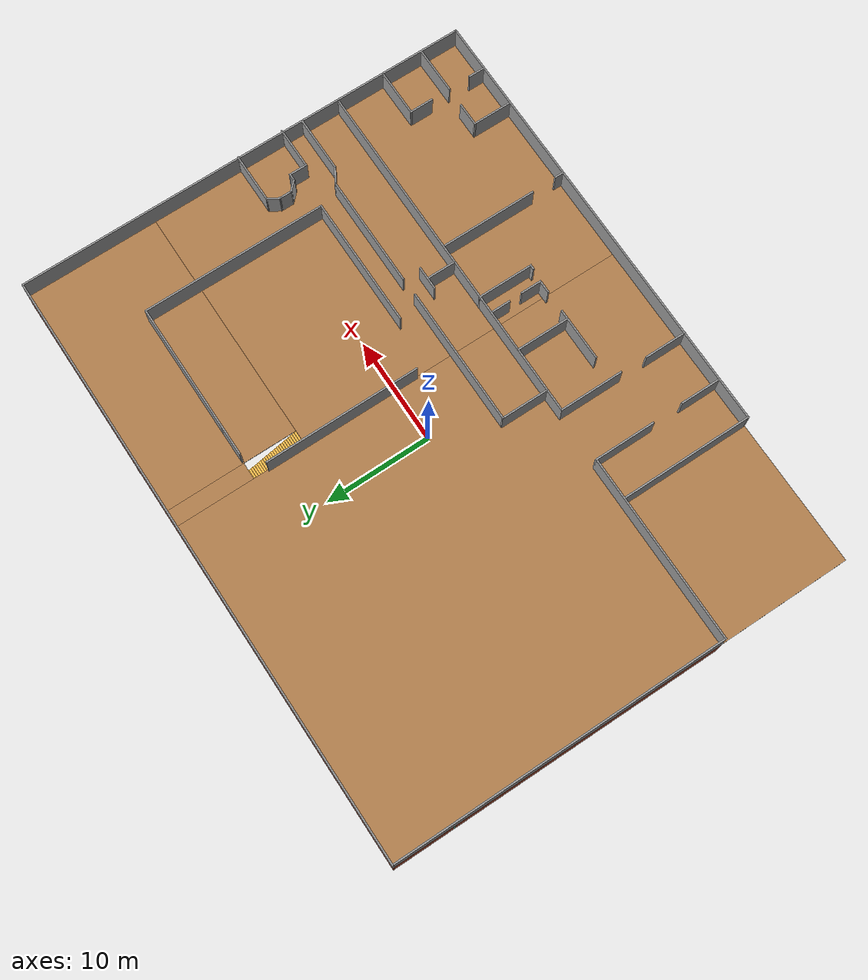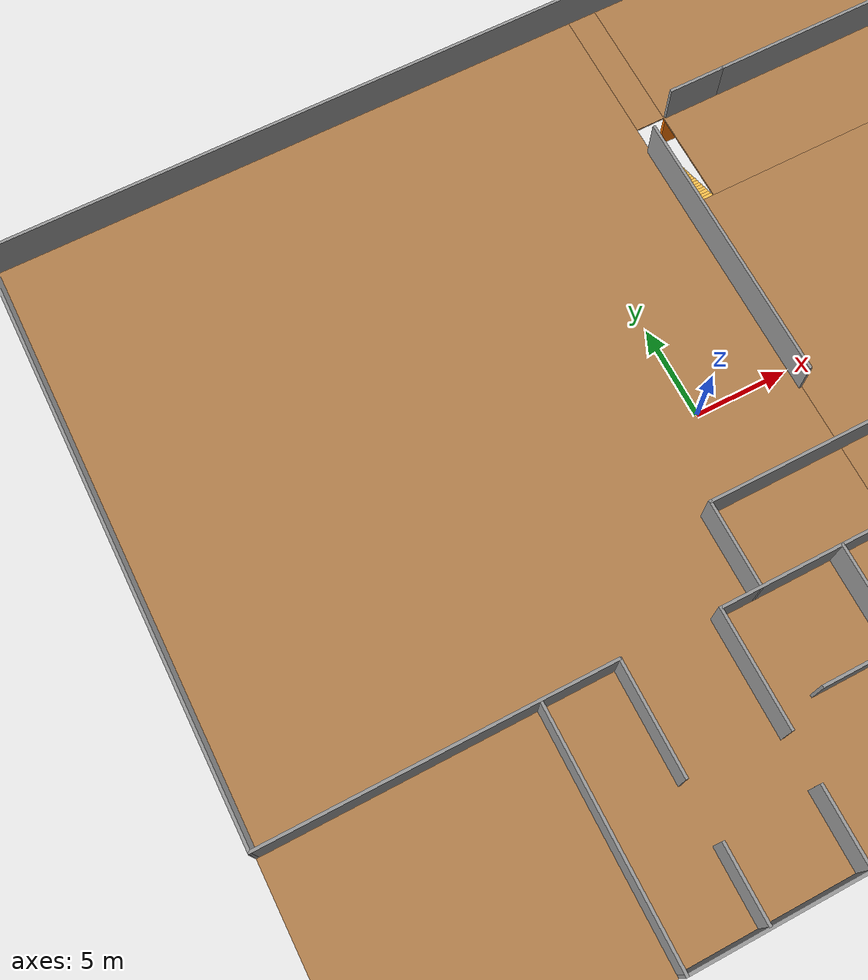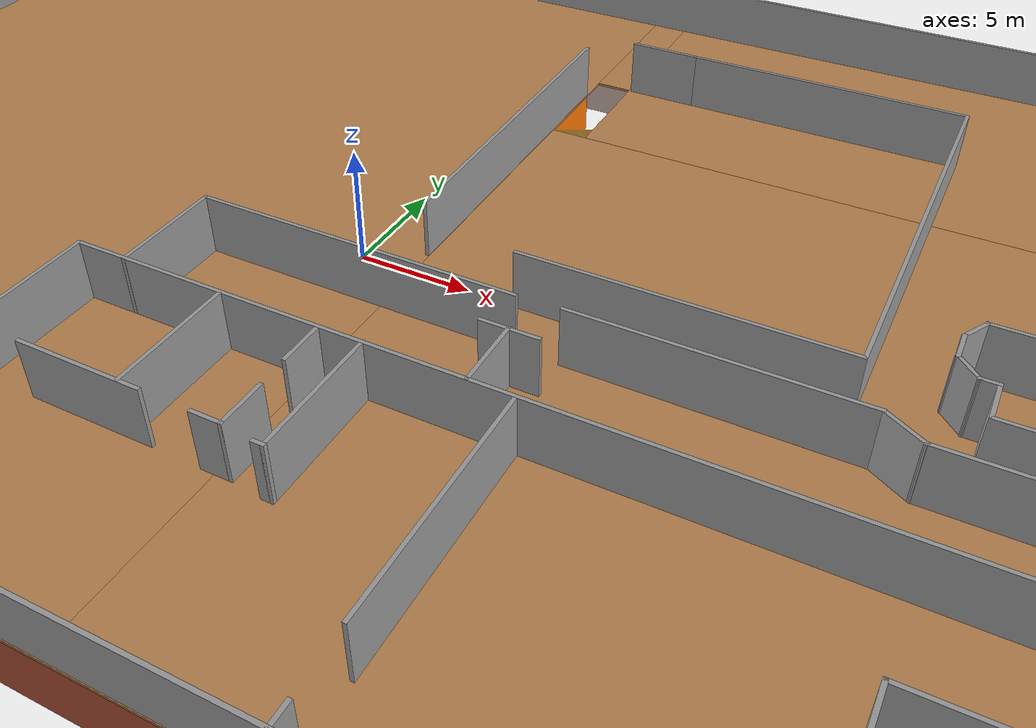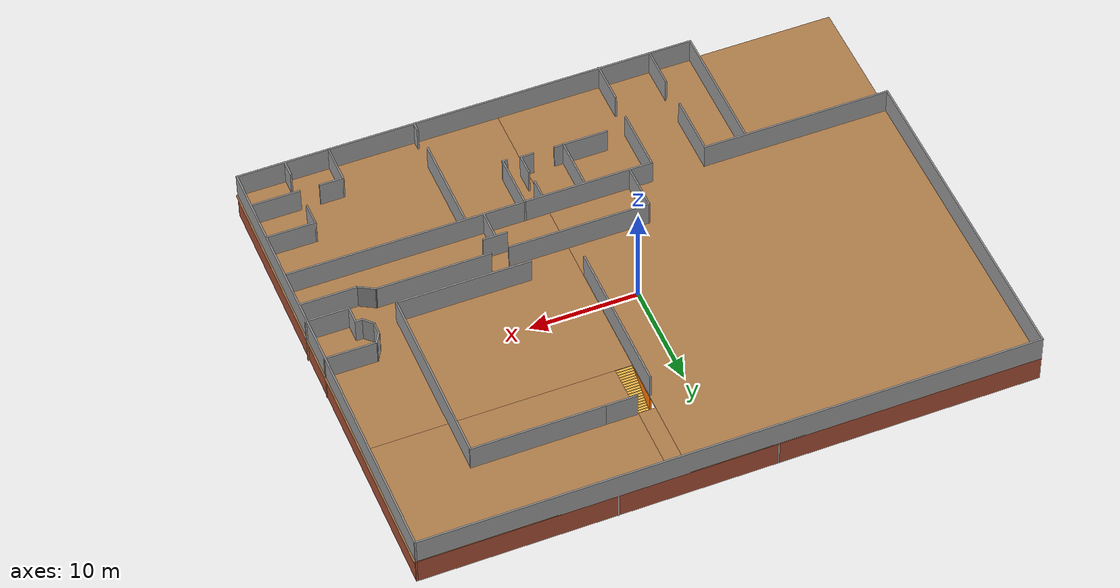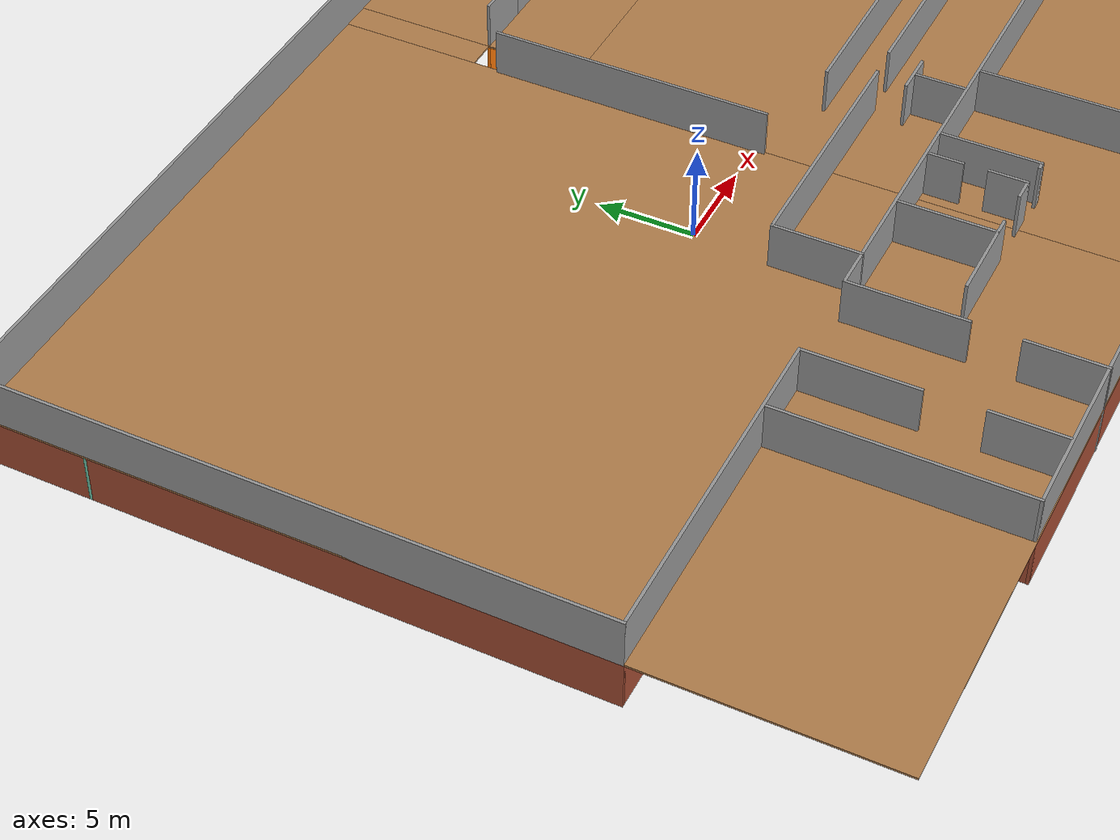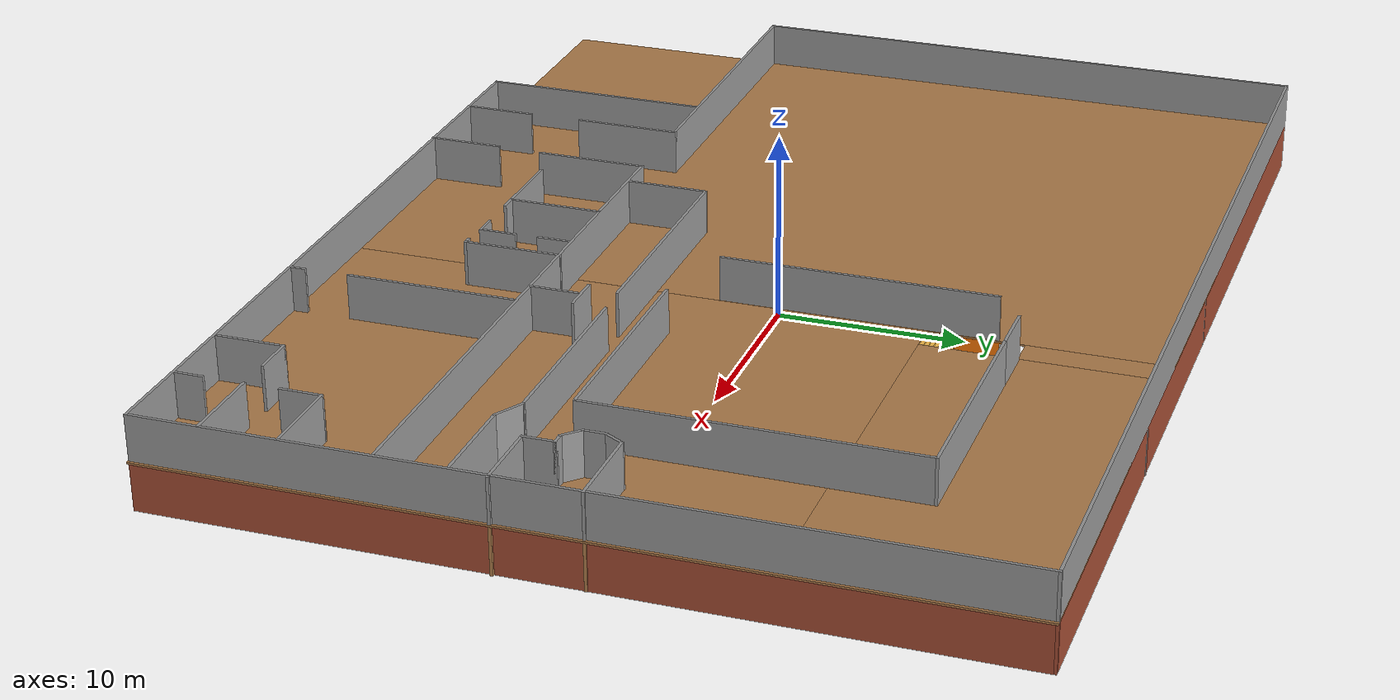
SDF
<?xml version='1.0'?>
<sdf version='1.7'>
  <model name='AKW'>
    <pose>0.485843 -0.100371 0 0 -0 0</pose>
    <link name='Floor_1'>
      <pose>0.000791 -0.015384 2.5 0 -0 0</pose>
      <visual name='Floor_1_Visual_0'>
        <pose>-12.1136 0 0.05 0 -0 0</pose>
        <geometry>
          <box>
            <size>31.911 43.2858 0.1</size>
          </box>
        </geometry>
        <material>
          <script>
            <uri>file://media/materials/scripts/gazebo.material</uri>
            <name>Gazebo/Wood</name>
          </script>
          <ambient>0.435294 0.796078 0.67451 1</ambient>
        </material>
        <meta>
          <layer>1</layer>
        </meta>
      </visual>
      <collision name='Floor_1_Collision_0'>
        <geometry>
          <box>
            <size>31.911 43.2858 0.1</size>
          </box>
        </geometry>
        <pose>-12.1136 0 0.05 0 -0 0</pose>
      </collision>
      <visual name='Floor_1_Visual_1'>
        <pose>15.9555 -6.20457 0.05 0 -0 0</pose>
        <geometry>
          <box>
            <size>24.2273 30.8766 0.1</size>
          </box>
        </geometry>
        <material>
          <script>
            <uri>file://media/materials/scripts/gazebo.material</uri>
            <name>Gazebo/Wood</name>
          </script>
          <ambient>0.435294 0.796078 0.67451 1</ambient>
        </material>
        <meta>
          <layer>1</layer>
        </meta>
      </visual>
      <collision name='Floor_1_Collision_1'>
        <geometry>
          <box>
            <size>24.2273 30.8766 0.1</size>
          </box>
        </geometry>
        <pose>15.9555 -6.20457 0.05 0 -0 0</pose>
      </collision>
      <visual name='Floor_1_Visual_2'>
        <pose>16.734 15.4383 0.05 0 -0 0</pose>
        <geometry>
          <box>
            <size>22.6703 12.4091 0.1</size>
          </box>
        </geometry>
        <material>
          <script>
            <uri>file://media/materials/scripts/gazebo.material</uri>
            <name>Gazebo/Wood</name>
          </script>
          <ambient>0.435294 0.796078 0.67451 1</ambient>
        </material>
        <meta>
          <layer>1</layer>
        </meta>
      </visual>
      <collision name='Floor_1_Collision_2'>
        <geometry>
          <box>
            <size>22.6703 12.4091 0.1</size>
          </box>
        </geometry>
        <pose>16.734 15.4383 0.05 0 -0 0</pose>
      </collision>
      <visual name='Floor_1_Visual_3'>
        <pose>4.62037 17.9383 0.05 0 -0 0</pose>
        <geometry>
          <box>
            <size>1.557 7.40913 0.1</size>
          </box>
        </geometry>
        <material>
          <script>
            <uri>file://media/materials/scripts/gazebo.material</uri>
            <name>Gazebo/Wood</name>
          </script>
          <ambient>0.435294 0.796078 0.67451 1</ambient>
        </material>
        <meta>
          <layer>1</layer>
        </meta>
      </visual>
      <collision name='Floor_1_Collision_3'>
        <geometry>
          <box>
            <size>1.557 7.40913 0.1</size>
          </box>
        </geometry>
        <pose>4.62037 17.9383 0.05 0 -0 0</pose>
      </collision>
    </link>
    <link name='Stairs_1'>
      <visual name='Stairs_1_Visual_0'>
        <pose>4.62116 14.1184 0.05 0 -0 0</pose>
        <geometry>
          <box>
            <size>1.557 0.2 0.1</size>
          </box>
        </geometry>
        <material>
          <script>
            <uri>file://media/materials/scripts/gazebo.material</uri>
            <name>Gazebo/Grey</name>
          </script>
          <ambient>1 0.764706 0.305882 1</ambient>
        </material>
        <meta>
          <layer>0</layer>
        </meta>
      </visual>
      <collision name='Stairs_1_Collision_0'>
        <geometry>
          <box>
            <size>1.557 0.2 0.1</size>
          </box>
        </geometry>
        <pose>4.62116 14.1184 0.05 0 -0 0</pose>
      </collision>
      <visual name='Stairs_1_Visual_1'>
        <pose>4.62116 13.9184 0.15 0 -0 0</pose>
        <geometry>
          <box>
            <size>1.557 0.2 0.1</size>
          </box>
        </geometry>
        <material>
          <script>
            <uri>file://media/materials/scripts/gazebo.material</uri>
            <name>Gazebo/Grey</name>
          </script>
          <ambient>1 0.764706 0.305882 1</ambient>
        </material>
        <meta>
          <layer>0</layer>
        </meta>
      </visual>
      <collision name='Stairs_1_Collision_1'>
        <geometry>
          <box>
            <size>1.557 0.2 0.1</size>
          </box>
        </geometry>
        <pose>4.62116 13.9184 0.15 0 -0 0</pose>
      </collision>
      <visual name='Stairs_1_Visual_2'>
        <pose>4.62116 13.7184 0.25 0 -0 0</pose>
        <geometry>
          <box>
            <size>1.557 0.2 0.1</size>
          </box>
        </geometry>
        <material>
          <script>
            <uri>file://media/materials/scripts/gazebo.material</uri>
            <name>Gazebo/Grey</name>
          </script>
          <ambient>1 0.764706 0.305882 1</ambient>
        </material>
        <meta>
          <layer>0</layer>
        </meta>
      </visual>
      <collision name='Stairs_1_Collision_2'>
        <geometry>
          <box>
            <size>1.557 0.2 0.1</size>
          </box>
        </geometry>
        <pose>4.62116 13.7184 0.25 0 -0 0</pose>
      </collision>
      <visual name='Stairs_1_Visual_3'>
        <pose>4.62116 13.5184 0.35 0 -0 0</pose>
        <geometry>
          <box>
            <size>1.557 0.2 0.1</size>
          </box>
        </geometry>
        <material>
          <script>
            <uri>file://media/materials/scripts/gazebo.material</uri>
            <name>Gazebo/Grey</name>
          </script>
          <ambient>1 0.764706 0.305882 1</ambient>
        </material>
        <meta>
          <layer>0</layer>
        </meta>
      </visual>
      <collision name='Stairs_1_Collision_3'>
        <geometry>
          <box>
            <size>1.557 0.2 0.1</size>
          </box>
        </geometry>
        <pose>4.62116 13.5184 0.35 0 -0 0</pose>
      </collision>
      <visual name='Stairs_1_Visual_4'>
        <pose>4.62116 13.3184 0.45 0 -0 0</pose>
        <geometry>
          <box>
            <size>1.557 0.2 0.1</size>
          </box>
        </geometry>
        <material>
          <script>
            <uri>file://media/materials/scripts/gazebo.material</uri>
            <name>Gazebo/Grey</name>
          </script>
          <ambient>1 0.764706 0.305882 1</ambient>
        </material>
        <meta>
          <layer>0</layer>
        </meta>
      </visual>
      <collision name='Stairs_1_Collision_4'>
        <geometry>
          <box>
            <size>1.557 0.2 0.1</size>
          </box>
        </geometry>
        <pose>4.62116 13.3184 0.45 0 -0 0</pose>
      </collision>
      <visual name='Stairs_1_Visual_5'>
        <pose>4.62116 13.1184 0.55 0 -0 0</pose>
        <geometry>
          <box>
            <size>1.557 0.2 0.1</size>
          </box>
        </geometry>
        <material>
          <script>
            <uri>file://media/materials/scripts/gazebo.material</uri>
            <name>Gazebo/Grey</name>
          </script>
          <ambient>1 0.764706 0.305882 1</ambient>
        </material>
        <meta>
          <layer>0</layer>
        </meta>
      </visual>
      <collision name='Stairs_1_Collision_5'>
        <geometry>
          <box>
            <size>1.557 0.2 0.1</size>
          </box>
        </geometry>
        <pose>4.62116 13.1184 0.55 0 -0 0</pose>
      </collision>
      <visual name='Stairs_1_Visual_6'>
        <pose>4.62116 12.9184 0.65 0 -0 0</pose>
        <geometry>
          <box>
            <size>1.557 0.2 0.1</size>
          </box>
        </geometry>
        <material>
          <script>
            <uri>file://media/materials/scripts/gazebo.material</uri>
            <name>Gazebo/Grey</name>
          </script>
          <ambient>1 0.764706 0.305882 1</ambient>
        </material>
        <meta>
          <layer>0</layer>
        </meta>
      </visual>
      <collision name='Stairs_1_Collision_6'>
        <geometry>
          <box>
            <size>1.557 0.2 0.1</size>
          </box>
        </geometry>
        <pose>4.62116 12.9184 0.65 0 -0 0</pose>
      </collision>
      <visual name='Stairs_1_Visual_7'>
        <pose>4.62116 12.7184 0.75 0 -0 0</pose>
        <geometry>
          <box>
            <size>1.557 0.2 0.1</size>
          </box>
        </geometry>
        <material>
          <script>
            <uri>file://media/materials/scripts/gazebo.material</uri>
            <name>Gazebo/Grey</name>
          </script>
          <ambient>1 0.764706 0.305882 1</ambient>
        </material>
        <meta>
          <layer>0</layer>
        </meta>
      </visual>
      <collision name='Stairs_1_Collision_7'>
        <geometry>
          <box>
            <size>1.557 0.2 0.1</size>
          </box>
        </geometry>
        <pose>4.62116 12.7184 0.75 0 -0 0</pose>
      </collision>
      <visual name='Stairs_1_Visual_8'>
        <pose>4.62116 12.5184 0.85 0 -0 0</pose>
        <geometry>
          <box>
            <size>1.557 0.2 0.1</size>
          </box>
        </geometry>
        <material>
          <script>
            <uri>file://media/materials/scripts/gazebo.material</uri>
            <name>Gazebo/Grey</name>
          </script>
          <ambient>1 0.764706 0.305882 1</ambient>
        </material>
        <meta>
          <layer>0</layer>
        </meta>
      </visual>
      <collision name='Stairs_1_Collision_8'>
        <geometry>
          <box>
            <size>1.557 0.2 0.1</size>
          </box>
        </geometry>
        <pose>4.62116 12.5184 0.85 0 -0 0</pose>
      </collision>
      <visual name='Stairs_1_Visual_9'>
        <pose>4.62116 12.3184 0.95 0 -0 0</pose>
        <geometry>
          <box>
            <size>1.557 0.2 0.1</size>
          </box>
        </geometry>
        <material>
          <script>
            <uri>file://media/materials/scripts/gazebo.material</uri>
            <name>Gazebo/Grey</name>
          </script>
          <ambient>1 0.764706 0.305882 1</ambient>
        </material>
        <meta>
          <layer>0</layer>
        </meta>
      </visual>
      <collision name='Stairs_1_Collision_9'>
        <geometry>
          <box>
            <size>1.557 0.2 0.1</size>
          </box>
        </geometry>
        <pose>4.62116 12.3184 0.95 0 -0 0</pose>
      </collision>
      <visual name='Stairs_1_Visual_10'>
        <pose>4.62116 12.1184 1.05 0 -0 0</pose>
        <geometry>
          <box>
            <size>1.557 0.2 0.1</size>
          </box>
        </geometry>
        <material>
          <script>
            <uri>file://media/materials/scripts/gazebo.material</uri>
            <name>Gazebo/Grey</name>
          </script>
          <ambient>1 0.764706 0.305882 1</ambient>
        </material>
        <meta>
          <layer>0</layer>
        </meta>
      </visual>
      <collision name='Stairs_1_Collision_10'>
        <geometry>
          <box>
            <size>1.557 0.2 0.1</size>
          </box>
        </geometry>
        <pose>4.62116 12.1184 1.05 0 -0 0</pose>
      </collision>
      <visual name='Stairs_1_Visual_11'>
        <pose>4.62116 11.9184 1.15 0 -0 0</pose>
        <geometry>
          <box>
            <size>1.557 0.2 0.1</size>
          </box>
        </geometry>
        <material>
          <script>
            <uri>file://media/materials/scripts/gazebo.material</uri>
            <name>Gazebo/Grey</name>
          </script>
          <ambient>1 0.764706 0.305882 1</ambient>
        </material>
        <meta>
          <layer>0</layer>
        </meta>
      </visual>
      <collision name='Stairs_1_Collision_11'>
        <geometry>
          <box>
            <size>1.557 0.2 0.1</size>
          </box>
        </geometry>
        <pose>4.62116 11.9184 1.15 0 -0 0</pose>
      </collision>
      <visual name='Stairs_1_Visual_12'>
        <pose>4.62116 11.7184 1.25 0 -0 0</pose>
        <geometry>
          <box>
            <size>1.557 0.2 0.1</size>
          </box>
        </geometry>
        <material>
          <script>
            <uri>file://media/materials/scripts/gazebo.material</uri>
            <name>Gazebo/Grey</name>
          </script>
          <ambient>1 0.764706 0.305882 1</ambient>
        </material>
        <meta>
          <layer>0</layer>
        </meta>
      </visual>
      <collision name='Stairs_1_Collision_12'>
        <geometry>
          <box>
            <size>1.557 0.2 0.1</size>
          </box>
        </geometry>
        <pose>4.62116 11.7184 1.25 0 -0 0</pose>
      </collision>
      <visual name='Stairs_1_Visual_13'>
        <pose>4.62116 11.5184 1.35 0 -0 0</pose>
        <geometry>
          <box>
            <size>1.557 0.2 0.1</size>
          </box>
        </geometry>
        <material>
          <script>
            <uri>file://media/materials/scripts/gazebo.material</uri>
            <name>Gazebo/Grey</name>
          </script>
          <ambient>1 0.764706 0.305882 1</ambient>
        </material>
        <meta>
          <layer>0</layer>
        </meta>
      </visual>
      <collision name='Stairs_1_Collision_13'>
        <geometry>
          <box>
            <size>1.557 0.2 0.1</size>
          </box>
        </geometry>
        <pose>4.62116 11.5184 1.35 0 -0 0</pose>
      </collision>
      <visual name='Stairs_1_Visual_14'>
        <pose>4.62116 11.3184 1.45 0 -0 0</pose>
        <geometry>
          <box>
            <size>1.557 0.2 0.1</size>
          </box>
        </geometry>
        <material>
          <script>
            <uri>file://media/materials/scripts/gazebo.material</uri>
            <name>Gazebo/Grey</name>
          </script>
          <ambient>1 0.764706 0.305882 1</ambient>
        </material>
        <meta>
          <layer>0</layer>
        </meta>
      </visual>
      <collision name='Stairs_1_Collision_14'>
        <geometry>
          <box>
            <size>1.557 0.2 0.1</size>
          </box>
        </geometry>
        <pose>4.62116 11.3184 1.45 0 -0 0</pose>
      </collision>
      <visual name='Stairs_1_Visual_15'>
        <pose>4.62116 11.1184 1.55 0 -0 0</pose>
        <geometry>
          <box>
            <size>1.557 0.2 0.1</size>
          </box>
        </geometry>
        <material>
          <script>
            <uri>file://media/materials/scripts/gazebo.material</uri>
            <name>Gazebo/Grey</name>
          </script>
          <ambient>1 0.764706 0.305882 1</ambient>
        </material>
        <meta>
          <layer>0</layer>
        </meta>
      </visual>
      <collision name='Stairs_1_Collision_15'>
        <geometry>
          <box>
            <size>1.557 0.2 0.1</size>
          </box>
        </geometry>
        <pose>4.62116 11.1184 1.55 0 -0 0</pose>
      </collision>
      <visual name='Stairs_1_Visual_16'>
        <pose>4.62116 10.9184 1.65 0 -0 0</pose>
        <geometry>
          <box>
            <size>1.557 0.2 0.1</size>
          </box>
        </geometry>
        <material>
          <script>
            <uri>file://media/materials/scripts/gazebo.material</uri>
            <name>Gazebo/Grey</name>
          </script>
          <ambient>1 0.764706 0.305882 1</ambient>
        </material>
        <meta>
          <layer>0</layer>
        </meta>
      </visual>
      <collision name='Stairs_1_Collision_16'>
        <geometry>
          <box>
            <size>1.557 0.2 0.1</size>
          </box>
        </geometry>
        <pose>4.62116 10.9184 1.65 0 -0 0</pose>
      </collision>
      <visual name='Stairs_1_Visual_17'>
        <pose>4.62116 10.7184 1.75 0 -0 0</pose>
        <geometry>
          <box>
            <size>1.557 0.2 0.1</size>
          </box>
        </geometry>
        <material>
          <script>
            <uri>file://media/materials/scripts/gazebo.material</uri>
            <name>Gazebo/Grey</name>
          </script>
          <ambient>1 0.764706 0.305882 1</ambient>
        </material>
        <meta>
          <layer>0</layer>
        </meta>
      </visual>
      <collision name='Stairs_1_Collision_17'>
        <geometry>
          <box>
            <size>1.557 0.2 0.1</size>
          </box>
        </geometry>
        <pose>4.62116 10.7184 1.75 0 -0 0</pose>
      </collision>
      <visual name='Stairs_1_Visual_18'>
        <pose>4.62116 10.5184 1.85 0 -0 0</pose>
        <geometry>
          <box>
            <size>1.557 0.2 0.1</size>
          </box>
        </geometry>
        <material>
          <script>
            <uri>file://media/materials/scripts/gazebo.material</uri>
            <name>Gazebo/Grey</name>
          </script>
          <ambient>1 0.764706 0.305882 1</ambient>
        </material>
        <meta>
          <layer>0</layer>
        </meta>
      </visual>
      <collision name='Stairs_1_Collision_18'>
        <geometry>
          <box>
            <size>1.557 0.2 0.1</size>
          </box>
        </geometry>
        <pose>4.62116 10.5184 1.85 0 -0 0</pose>
      </collision>
      <visual name='Stairs_1_Visual_19'>
        <pose>4.62116 10.3184 1.95 0 -0 0</pose>
        <geometry>
          <box>
            <size>1.557 0.2 0.1</size>
          </box>
        </geometry>
        <material>
          <script>
            <uri>file://media/materials/scripts/gazebo.material</uri>
            <name>Gazebo/Grey</name>
          </script>
          <ambient>1 0.764706 0.305882 1</ambient>
        </material>
        <meta>
          <layer>0</layer>
        </meta>
      </visual>
      <collision name='Stairs_1_Collision_19'>
        <geometry>
          <box>
            <size>1.557 0.2 0.1</size>
          </box>
        </geometry>
        <pose>4.62116 10.3184 1.95 0 -0 0</pose>
      </collision>
      <visual name='Stairs_1_Visual_20'>
        <pose>4.62116 10.1184 2.05 0 -0 0</pose>
        <geometry>
          <box>
            <size>1.557 0.2 0.1</size>
          </box>
        </geometry>
        <material>
          <script>
            <uri>file://media/materials/scripts/gazebo.material</uri>
            <name>Gazebo/Grey</name>
          </script>
          <ambient>1 0.764706 0.305882 1</ambient>
        </material>
        <meta>
          <layer>0</layer>
        </meta>
      </visual>
      <collision name='Stairs_1_Collision_20'>
        <geometry>
          <box>
            <size>1.557 0.2 0.1</size>
          </box>
        </geometry>
        <pose>4.62116 10.1184 2.05 0 -0 0</pose>
      </collision>
      <visual name='Stairs_1_Visual_21'>
        <pose>4.62116 9.91837 2.15 0 -0 0</pose>
        <geometry>
          <box>
            <size>1.557 0.2 0.1</size>
          </box>
        </geometry>
        <material>
          <script>
            <uri>file://media/materials/scripts/gazebo.material</uri>
            <name>Gazebo/Grey</name>
          </script>
          <ambient>1 0.764706 0.305882 1</ambient>
        </material>
        <meta>
          <layer>0</layer>
        </meta>
      </visual>
      <collision name='Stairs_1_Collision_21'>
        <geometry>
          <box>
            <size>1.557 0.2 0.1</size>
          </box>
        </geometry>
        <pose>4.62116 9.91837 2.15 0 -0 0</pose>
      </collision>
      <visual name='Stairs_1_Visual_22'>
        <pose>4.62116 9.71837 2.25 0 -0 0</pose>
        <geometry>
          <box>
            <size>1.557 0.2 0.1</size>
          </box>
        </geometry>
        <material>
          <script>
            <uri>file://media/materials/scripts/gazebo.material</uri>
            <name>Gazebo/Grey</name>
          </script>
          <ambient>1 0.764706 0.305882 1</ambient>
        </material>
        <meta>
          <layer>0</layer>
        </meta>
      </visual>
      <collision name='Stairs_1_Collision_22'>
        <geometry>
          <box>
            <size>1.557 0.2 0.1</size>
          </box>
        </geometry>
        <pose>4.62116 9.71837 2.25 0 -0 0</pose>
      </collision>
      <visual name='Stairs_1_Visual_23'>
        <pose>4.62116 9.51837 2.35 0 -0 0</pose>
        <geometry>
          <box>
            <size>1.557 0.2 0.1</size>
          </box>
        </geometry>
        <material>
          <script>
            <uri>file://media/materials/scripts/gazebo.material</uri>
            <name>Gazebo/Grey</name>
          </script>
          <ambient>1 0.764706 0.305882 1</ambient>
        </material>
        <meta>
          <layer>0</layer>
        </meta>
      </visual>
      <collision name='Stairs_1_Collision_23'>
        <geometry>
          <box>
            <size>1.557 0.2 0.1</size>
          </box>
        </geometry>
        <pose>4.62116 9.51837 2.35 0 -0 0</pose>
      </collision>
      <visual name='Stairs_1_Visual_24'>
        <pose>4.62116 9.31837 2.45 0 -0 0</pose>
        <geometry>
          <box>
            <size>1.557 0.2 0.1</size>
          </box>
        </geometry>
        <material>
          <script>
            <uri>file://media/materials/scripts/gazebo.material</uri>
            <name>Gazebo/Grey</name>
          </script>
          <ambient>1 0.764706 0.305882 1</ambient>
        </material>
        <meta>
          <layer>0</layer>
        </meta>
      </visual>
      <collision name='Stairs_1_Collision_24'>
        <geometry>
          <box>
            <size>1.557 0.2 0.1</size>
          </box>
        </geometry>
        <pose>4.62116 9.31837 2.45 0 -0 0</pose>
      </collision>
    </link>
    <link name='Wall_0'>
      <collision name='Wall_0_Collision'>
        <geometry>
          <box>
            <size>42.5 0.15 2.5</size>
          </box>
        </geometry>
        <pose>0 0 1.25 0 -0 0</pose>
      </collision>
      <visual name='Wall_0_Visual'>
        <pose>0 0 1.25 0 -0 0</pose>
        <geometry>
          <box>
            <size>42.5 0.15 2.5</size>
          </box>
        </geometry>
        <material>
          <script>
            <uri>file://media/materials/scripts/gazebo.material</uri>
            <name>Gazebo/Bricks</name>
          </script>
          <ambient>1 1 1 1</ambient>
        </material>
        <meta>
          <layer>0</layer>
        </meta>
      </visual>
      <pose>6.68165 -21.5475 0 0 -0 0</pose>
    </link>
    <link name='Wall_1'>
      <collision name='Wall_1_Collision'>
        <geometry>
          <box>
            <size>43.25 0.15 2.5</size>
          </box>
        </geometry>
        <pose>0 0 1.25 0 -0 0</pose>
      </collision>
      <visual name='Wall_1_Visual'>
        <pose>0 0 1.25 0 -0 0</pose>
        <geometry>
          <box>
            <size>43.25 0.15 2.5</size>
          </box>
        </geometry>
        <material>
          <script>
            <uri>file://media/materials/scripts/gazebo.material</uri>
            <name>Gazebo/Bricks</name>
          </script>
          <ambient>1 1 1 1</ambient>
        </material>
        <meta>
          <layer>0</layer>
        </meta>
      </visual>
      <pose>27.8567 0.002503 0 0 -0 1.5708</pose>
    </link>
    <link name='Wall_10'>
      <collision name='Wall_10_Collision'>
        <geometry>
          <box>
            <size>33.5 0.15 2.5</size>
          </box>
        </geometry>
        <pose>0 0 1.25 0 -0 0</pose>
      </collision>
      <visual name='Wall_10_Visual'>
        <pose>0 0 1.25 0 -0 0</pose>
        <geometry>
          <box>
            <size>33.5 0.15 2.5</size>
          </box>
        </geometry>
        <material>
          <script>
            <uri>file://media/materials/scripts/gazebo.material</uri>
            <name>Gazebo/CeilingTiled</name>
          </script>
          <ambient>1 1 1 1</ambient>
        </material>
        <meta>
          <layer>0</layer>
        </meta>
      </visual>
      <pose>10.9914 -9.37368 0 0 -0 0</pose>
    </link>
    <link name='Wall_100'>
      <collision name='Wall_100_Collision'>
        <geometry>
          <box>
            <size>4.75 0.15 2.5</size>
          </box>
        </geometry>
        <pose>0 0 1.25 0 -0 0</pose>
      </collision>
      <visual name='Wall_100_Visual'>
        <pose>0 0 1.25 0 -0 0</pose>
        <geometry>
          <box>
            <size>4.75 0.15 2.5</size>
          </box>
        </geometry>
        <material>
          <script>
            <uri>file://media/materials/scripts/gazebo.material</uri>
            <name>Gazebo/Wood</name>
          </script>
          <ambient>1 1 1 1</ambient>
        </material>
        <meta>
          <layer>0</layer>
        </meta>
      </visual>
      <pose>25.6171 0.610399 0 0 -0 3.14159</pose>
    </link>
    <link name='Wall_101'>
      <collision name='Wall_101_Collision'>
        <geometry>
          <box>
            <size>1.25 0.15 2.5</size>
          </box>
        </geometry>
        <pose>0 0 1.25 0 -0 0</pose>
      </collision>
      <visual name='Wall_101_Visual'>
        <pose>0 0 1.25 0 -0 0</pose>
        <geometry>
          <box>
            <size>1.25 0.15 2.5</size>
          </box>
        </geometry>
        <material>
          <script>
            <uri>file://media/materials/scripts/gazebo.material</uri>
            <name>Gazebo/Wood</name>
          </script>
          <ambient>1 1 1 1</ambient>
        </material>
        <meta>
          <layer>0</layer>
        </meta>
      </visual>
      <pose>23.0421 0.134085 0 0 -0 -2.0944</pose>
    </link>
    <link name='Wall_102'>
      <collision name='Wall_102_Collision'>
        <geometry>
          <box>
            <size>1.25 0.15 2.5</size>
          </box>
        </geometry>
        <pose>0 0 1.25 0 -0 0</pose>
      </collision>
      <visual name='Wall_102_Visual'>
        <pose>0 0 1.25 0 -0 0</pose>
        <geometry>
          <box>
            <size>1.25 0.15 2.5</size>
          </box>
        </geometry>
        <material>
          <script>
            <uri>file://media/materials/scripts/gazebo.material</uri>
            <name>Gazebo/Wood</name>
          </script>
          <ambient>1 1 1 1</ambient>
        </material>
        <meta>
          <layer>0</layer>
        </meta>
      </visual>
      <pose>22.7671 -0.892229 0 0 -0 -1.5708</pose>
    </link>
    <link name='Wall_103'>
      <collision name='Wall_103_Collision'>
        <geometry>
          <box>
            <size>1.25 0.15 2.5</size>
          </box>
        </geometry>
        <pose>0 0 1.25 0 -0 0</pose>
      </collision>
      <visual name='Wall_103_Visual'>
        <pose>0 0 1.25 0 -0 0</pose>
        <geometry>
          <box>
            <size>1.25 0.15 2.5</size>
          </box>
        </geometry>
        <material>
          <script>
            <uri>file://media/materials/scripts/gazebo.material</uri>
            <name>Gazebo/Wood</name>
          </script>
          <ambient>1 1 1 1</ambient>
        </material>
        <meta>
          <layer>0</layer>
        </meta>
      </visual>
      <pose>23.156 -1.83114 0 0 -0 -0.785398</pose>
    </link>
    <link name='Wall_104'>
      <collision name='Wall_104_Collision'>
        <geometry>
          <box>
            <size>0.75 0.15 2.5</size>
          </box>
        </geometry>
        <pose>0 0 1.25 0 -0 0</pose>
      </collision>
      <visual name='Wall_104_Visual'>
        <pose>0 0 1.25 0 -0 0</pose>
        <geometry>
          <box>
            <size>0.75 0.15 2.5</size>
          </box>
        </geometry>
        <material>
          <script>
            <uri>file://media/materials/scripts/gazebo.material</uri>
            <name>Gazebo/Wood</name>
          </script>
          <ambient>1 1 1 1</ambient>
        </material>
        <meta>
          <layer>0</layer>
        </meta>
      </visual>
      <pose>23.8449 -2.22005 0 0 -0 0</pose>
    </link>
    <link name='Wall_105'>
      <collision name='Wall_105_Collision'>
        <geometry>
          <box>
            <size>1.75 0.15 2.5</size>
          </box>
        </geometry>
        <pose>0 0 1.25 0 -0 0</pose>
      </collision>
      <visual name='Wall_105_Visual'>
        <pose>0 0 1.25 0 -0 0</pose>
        <geometry>
          <box>
            <size>1.75 0.15 2.5</size>
          </box>
        </geometry>
        <material>
          <script>
            <uri>file://media/materials/scripts/gazebo.material</uri>
            <name>Gazebo/Wood</name>
          </script>
          <ambient>1 1 1 1</ambient>
        </material>
        <meta>
          <layer>0</layer>
        </meta>
      </visual>
      <pose>24.1449 -3.02005 0 0 -0 -1.5708</pose>
    </link>
    <link name='Wall_106'>
      <collision name='Wall_106_Collision'>
        <geometry>
          <box>
            <size>4 0.15 2.5</size>
          </box>
        </geometry>
        <pose>0 0 1.25 0 -0 0</pose>
      </collision>
      <visual name='Wall_106_Visual'>
        <pose>0 0 1.25 0 -0 0</pose>
        <geometry>
          <box>
            <size>4 0.15 2.5</size>
          </box>
        </geometry>
        <material>
          <script>
            <uri>file://media/materials/scripts/gazebo.material</uri>
            <name>Gazebo/Wood</name>
          </script>
          <ambient>1 1 1 1</ambient>
        </material>
        <meta>
          <layer>0</layer>
        </meta>
      </visual>
      <pose>26.0699 -3.82005 0 0 -0 0</pose>
    </link>
    <link name='Wall_108'>
      <collision name='Wall_108_Collision'>
        <geometry>
          <box>
            <size>5 0.15 2.5</size>
          </box>
        </geometry>
        <pose>0 0 1.25 0 -0 0</pose>
      </collision>
      <visual name='Wall_108_Visual'>
        <pose>0 0 1.25 0 -0 0</pose>
        <geometry>
          <box>
            <size>5 0.15 2.5</size>
          </box>
        </geometry>
        <material>
          <script>
            <uri>file://media/materials/scripts/gazebo.material</uri>
            <name>Gazebo/Grey</name>
          </script>
          <ambient>0.996078 0.47451 0.0196078 1</ambient>
        </material>
        <meta>
          <layer>0</layer>
        </meta>
      </visual>
      <pose>-1.29696 12.7755 0 0 -0 3.14159</pose>
    </link>
    <link name='Wall_109'>
      <collision name='Wall_109_Collision'>
        <geometry>
          <box>
            <size>7 0.15 2.5</size>
          </box>
        </geometry>
        <pose>0 0 1.25 0 -0 0</pose>
      </collision>
      <visual name='Wall_109_Visual'>
        <pose>0 0 1.25 0 -0 0</pose>
        <geometry>
          <box>
            <size>7 0.15 2.5</size>
          </box>
        </geometry>
        <material>
          <script>
            <uri>file://media/materials/scripts/gazebo.material</uri>
            <name>Gazebo/Grey</name>
          </script>
          <ambient>0.996078 0.47451 0.0196078 1</ambient>
        </material>
        <meta>
          <layer>0</layer>
        </meta>
      </visual>
      <pose>-3.72196 9.35053 0 0 -0 -1.5708</pose>
    </link>
    <link name='Wall_110'>
      <collision name='Wall_110_Collision'>
        <geometry>
          <box>
            <size>2 0.15 2.5</size>
          </box>
        </geometry>
        <pose>0 0 1.25 0 -0 0</pose>
      </collision>
      <visual name='Wall_110_Visual'>
        <pose>0 0 1.25 0 -0 0</pose>
        <geometry>
          <box>
            <size>2 0.15 2.5</size>
          </box>
        </geometry>
        <material>
          <script>
            <uri>file://media/materials/scripts/gazebo.material</uri>
            <name>Gazebo/Grey</name>
          </script>
          <ambient>0.996078 0.47451 0.0196078 1</ambient>
        </material>
        <meta>
          <layer>0</layer>
        </meta>
      </visual>
      <pose>-4.64696 5.92553 0 0 -0 3.14159</pose>
    </link>
    <link name='Wall_111'>
      <collision name='Wall_111_Collision'>
        <geometry>
          <box>
            <size>5 0.15 2.5</size>
          </box>
        </geometry>
        <pose>0 0 1.25 0 -0 0</pose>
      </collision>
      <visual name='Wall_111_Visual'>
        <pose>0 0 1.25 0 -0 0</pose>
        <geometry>
          <box>
            <size>5 0.15 2.5</size>
          </box>
        </geometry>
        <material>
          <script>
            <uri>file://media/materials/scripts/gazebo.material</uri>
            <name>Gazebo/Grey</name>
          </script>
          <ambient>0.996078 0.47451 0.0196078 1</ambient>
        </material>
        <meta>
          <layer>0</layer>
        </meta>
      </visual>
      <pose>-5.57196 8.35053 0 0 -0 1.5708</pose>
    </link>
    <link name='Wall_112'>
      <collision name='Wall_112_Collision'>
        <geometry>
          <box>
            <size>2 0.15 2.5</size>
          </box>
        </geometry>
        <pose>0 0 1.25 0 -0 0</pose>
      </collision>
      <visual name='Wall_112_Visual'>
        <pose>0 0 1.25 0 -0 0</pose>
        <geometry>
          <box>
            <size>2 0.15 2.5</size>
          </box>
        </geometry>
        <material>
          <script>
            <uri>file://media/materials/scripts/gazebo.material</uri>
            <name>Gazebo/Grey</name>
          </script>
          <ambient>0.996078 0.47451 0.0196078 1</ambient>
        </material>
        <meta>
          <layer>0</layer>
        </meta>
      </visual>
      <pose>-4.64696 10.7755 0 0 -0 0</pose>
    </link>
    <link name='Wall_114'>
      <collision name='Wall_114_Collision'>
        <geometry>
          <box>
            <size>2 0.15 2.5</size>
          </box>
        </geometry>
        <pose>0 0 1.25 0 -0 0</pose>
      </collision>
      <visual name='Wall_114_Visual'>
        <pose>0 0 1.25 0 -0 0</pose>
        <geometry>
          <box>
            <size>2 0.15 2.5</size>
          </box>
        </geometry>
        <material>
          <script>
            <uri>file://media/materials/scripts/gazebo.material</uri>
            <name>Gazebo/Grey</name>
          </script>
          <ambient>0.996078 0.47451 0.0196078 1</ambient>
        </material>
        <meta>
          <layer>0</layer>
        </meta>
      </visual>
      <pose>-2.79696 10.7755 0 0 -0 0</pose>
    </link>
    <link name='Wall_115'>
      <collision name='Wall_115_Collision'>
        <geometry>
          <box>
            <size>1.25 0.15 2.5</size>
          </box>
        </geometry>
        <pose>0 0 1.25 0 -0 0</pose>
      </collision>
      <visual name='Wall_115_Visual'>
        <pose>0 0 1.25 0 -0 0</pose>
        <geometry>
          <box>
            <size>1.25 0.15 2.5</size>
          </box>
        </geometry>
        <material>
          <script>
            <uri>file://media/materials/scripts/gazebo.material</uri>
            <name>Gazebo/Grey</name>
          </script>
          <ambient>0.996078 0.47451 0.0196078 1</ambient>
        </material>
        <meta>
          <layer>0</layer>
        </meta>
      </visual>
      <pose>-1.39565 11.0505 0 0 -0 0.523599</pose>
    </link>
    <link name='Wall_116'>
      <collision name='Wall_116_Collision'>
        <geometry>
          <box>
            <size>1.5 0.15 2.5</size>
          </box>
        </geometry>
        <pose>0 0 1.25 0 -0 0</pose>
      </collision>
      <visual name='Wall_116_Visual'>
        <pose>0 0 1.25 0 -0 0</pose>
        <geometry>
          <box>
            <size>1.5 0.15 2.5</size>
          </box>
        </geometry>
        <material>
          <script>
            <uri>file://media/materials/scripts/gazebo.material</uri>
            <name>Gazebo/Grey</name>
          </script>
          <ambient>0.996078 0.47451 0.0196078 1</ambient>
        </material>
        <meta>
          <layer>0</layer>
        </meta>
      </visual>
      <pose>-0.919332 12.0005 0 0 -0 1.5708</pose>
    </link>
    <link name='Wall_118'>
      <collision name='Wall_118_Collision'>
        <geometry>
          <box>
            <size>14.5 0.15 2.5</size>
          </box>
        </geometry>
        <pose>0 0 1.25 0 -0 0</pose>
      </collision>
      <visual name='Wall_118_Visual'>
        <pose>0 0 1.25 0 -0 0</pose>
        <geometry>
          <box>
            <size>14.5 0.15 2.5</size>
          </box>
        </geometry>
        <material>
          <script>
            <uri>file://media/materials/scripts/gazebo.material</uri>
            <name>Gazebo/Grey</name>
          </script>
          <ambient>0.996078 0.47451 0.0196078 1</ambient>
        </material>
        <meta>
          <layer>0</layer>
        </meta>
      </visual>
      <pose>3.74669 5.6278 0 0 -0 -1.5708</pose>
    </link>
    <link name='Wall_119'>
      <collision name='Wall_119_Collision'>
        <geometry>
          <box>
            <size>7.75 0.15 2.5</size>
          </box>
        </geometry>
        <pose>0 0 1.25 0 -0 0</pose>
      </collision>
      <visual name='Wall_119_Visual'>
        <pose>0 0 1.25 0 -0 0</pose>
        <geometry>
          <box>
            <size>7.75 0.15 2.5</size>
          </box>
        </geometry>
        <material>
          <script>
            <uri>file://media/materials/scripts/gazebo.material</uri>
            <name>Gazebo/Grey</name>
          </script>
          <ambient>0.996078 0.47451 0.0196078 1</ambient>
        </material>
        <meta>
          <layer>0</layer>
        </meta>
      </visual>
      <pose>-0.053314 -1.5472 0 0 -0 3.14159</pose>
    </link>
    <link name='Wall_12'>
      <collision name='Wall_12_Collision'>
        <geometry>
          <box>
            <size>19 0.15 2.5</size>
          </box>
        </geometry>
        <pose>0 0 1.25 0 -0 0</pose>
      </collision>
      <visual name='Wall_12_Visual'>
        <pose>0 0 1.25 0 -0 0</pose>
        <geometry>
          <box>
            <size>19 0.15 2.5</size>
          </box>
        </geometry>
        <material>
          <script>
            <uri>file://media/materials/scripts/gazebo.material</uri>
            <name>Gazebo/Bricks</name>
          </script>
          <ambient>1 1 1 1</ambient>
        </material>
        <meta>
          <layer>0</layer>
        </meta>
      </visual>
      <pose>-10.8959 4.66757 0 0 -0 1.5708</pose>
    </link>
    <link name='Wall_120'>
      <collision name='Wall_120_Collision'>
        <geometry>
          <box>
            <size>4.25 0.15 2.5</size>
          </box>
        </geometry>
        <pose>0 0 1.25 0 -0 0</pose>
      </collision>
      <visual name='Wall_120_Visual'>
        <pose>0 0 1.25 0 -0 0</pose>
        <geometry>
          <box>
            <size>4.25 0.15 2.5</size>
          </box>
        </geometry>
        <material>
          <script>
            <uri>file://media/materials/scripts/gazebo.material</uri>
            <name>Gazebo/Grey</name>
          </script>
          <ambient>0.996078 0.47451 0.0196078 1</ambient>
        </material>
        <meta>
          <layer>0</layer>
        </meta>
      </visual>
      <pose>-3.85331 0.502804 0 0 -0 1.5708</pose>
    </link>
    <link name='Wall_121'>
      <collision name='Wall_121_Collision'>
        <geometry>
          <box>
            <size>2 0.15 2.5</size>
          </box>
        </geometry>
        <pose>0 0 1.25 0 -0 0</pose>
      </collision>
      <visual name='Wall_121_Visual'>
        <pose>0 0 1.25 0 -0 0</pose>
        <geometry>
          <box>
            <size>2 0.15 2.5</size>
          </box>
        </geometry>
        <material>
          <script>
            <uri>file://media/materials/scripts/gazebo.material</uri>
            <name>Gazebo/Grey</name>
          </script>
          <ambient>0.996078 0.47451 0.0196078 1</ambient>
        </material>
        <meta>
          <layer>0</layer>
        </meta>
      </visual>
      <pose>-2.92831 2.5528 0 0 -0 0</pose>
    </link>
    <link name='Wall_122'>
      <collision name='Wall_122_Collision'>
        <geometry>
          <box>
            <size>0.75 0.15 2.5</size>
          </box>
        </geometry>
        <pose>0 0 1.25 0 -0 0</pose>
      </collision>
      <visual name='Wall_122_Visual'>
        <pose>0 0 1.25 0 -0 0</pose>
        <geometry>
          <box>
            <size>0.75 0.15 2.5</size>
          </box>
        </geometry>
        <material>
          <script>
            <uri>file://media/materials/scripts/gazebo.material</uri>
            <name>Gazebo/Grey</name>
          </script>
          <ambient>0.996078 0.47451 0.0196078 1</ambient>
        </material>
        <meta>
          <layer>0</layer>
        </meta>
      </visual>
      <pose>-1.79118 2.34067 0 0 -0 -0.785398</pose>
    </link>
    <link name='Wall_123'>
      <collision name='Wall_123_Collision'>
        <geometry>
          <box>
            <size>2 0.15 2.5</size>
          </box>
        </geometry>
        <pose>0 0 1.25 0 -0 0</pose>
      </collision>
      <visual name='Wall_123_Visual'>
        <pose>0 0 1.25 0 -0 0</pose>
        <geometry>
          <box>
            <size>2 0.15 2.5</size>
          </box>
        </geometry>
        <material>
          <script>
            <uri>file://media/materials/scripts/gazebo.material</uri>
            <name>Gazebo/Grey</name>
          </script>
          <ambient>0.996078 0.47451 0.0196078 1</ambient>
        </material>
        <meta>
          <layer>0</layer>
        </meta>
      </visual>
      <pose>-1.57905 1.20354 0 0 -0 -1.5708</pose>
    </link>
    <link name='Wall_124'>
      <collision name='Wall_124_Collision'>
        <geometry>
          <box>
            <size>1 0.15 2.5</size>
          </box>
        </geometry>
        <pose>0 0 1.25 0 -0 0</pose>
      </collision>
      <visual name='Wall_124_Visual'>
        <pose>0 0 1.25 0 -0 0</pose>
        <geometry>
          <box>
            <size>1 0.15 2.5</size>
          </box>
        </geometry>
        <material>
          <script>
            <uri>file://media/materials/scripts/gazebo.material</uri>
            <name>Gazebo/Grey</name>
          </script>
          <ambient>0.996078 0.47451 0.0196078 1</ambient>
        </material>
        <meta>
          <layer>0</layer>
        </meta>
      </visual>
      <pose>-1.15405 0.27854 0 0 -0 0</pose>
    </link>
    <link name='Wall_125'>
      <collision name='Wall_125_Collision'>
        <geometry>
          <box>
            <size>1.75 0.15 2.5</size>
          </box>
        </geometry>
        <pose>0 0 1.25 0 -0 0</pose>
      </collision>
      <visual name='Wall_125_Visual'>
        <pose>0 0 1.25 0 -0 0</pose>
        <geometry>
          <box>
            <size>1.75 0.15 2.5</size>
          </box>
        </geometry>
        <material>
          <script>
            <uri>file://media/materials/scripts/gazebo.material</uri>
            <name>Gazebo/Grey</name>
          </script>
          <ambient>0.996078 0.47451 0.0196078 1</ambient>
        </material>
        <meta>
          <layer>0</layer>
        </meta>
      </visual>
      <pose>-0.729049 -0.52146 0 0 -0 -1.5708</pose>
    </link>
    <link name='Wall_126'>
      <collision name='Wall_126_Collision'>
        <geometry>
          <box>
            <size>0.25 0.15 2.5</size>
          </box>
        </geometry>
        <pose>0 0 1.25 0 -0 0</pose>
      </collision>
      <visual name='Wall_126_Visual'>
        <pose>0 0 1.25 0 -0 0</pose>
        <geometry>
          <box>
            <size>0.25 0.15 2.5</size>
          </box>
        </geometry>
        <material>
          <script>
            <uri>file://media/materials/scripts/gazebo.material</uri>
            <name>Gazebo/Grey</name>
          </script>
          <ambient>0.996078 0.47451 0.0196078 1</ambient>
        </material>
        <meta>
          <layer>0</layer>
        </meta>
      </visual>
      <pose>-0.729049 -1.37146 0 0 -0 -1.5708</pose>
    </link>
    <link name='Wall_128'>
      <collision name='Wall_128_Collision'>
        <geometry>
          <box>
            <size>3.25 0.15 2.5</size>
          </box>
        </geometry>
        <pose>0 0 1.25 0 -0 0</pose>
      </collision>
      <visual name='Wall_128_Visual'>
        <pose>0 0 1.25 0 -0 0</pose>
        <geometry>
          <box>
            <size>3.25 0.15 2.5</size>
          </box>
        </geometry>
        <material>
          <script>
            <uri>file://media/materials/scripts/gazebo.material</uri>
            <name>Gazebo/Grey</name>
          </script>
          <ambient>0.996078 0.47451 0.0196078 1</ambient>
        </material>
        <meta>
          <layer>0</layer>
        </meta>
      </visual>
      <pose>5.29669 -1.5472 0 0 -0 0</pose>
    </link>
    <link name='Wall_129'>
      <collision name='Wall_129_Collision'>
        <geometry>
          <box>
            <size>2 0.15 2.5</size>
          </box>
        </geometry>
        <pose>0 0 1.25 0 -0 0</pose>
      </collision>
      <visual name='Wall_129_Visual'>
        <pose>0 0 1.25 0 -0 0</pose>
        <geometry>
          <box>
            <size>2 0.15 2.5</size>
          </box>
        </geometry>
        <material>
          <script>
            <uri>file://media/materials/scripts/gazebo.material</uri>
            <name>Gazebo/Grey</name>
          </script>
          <ambient>0.996078 0.47451 0.0196078 1</ambient>
        </material>
        <meta>
          <layer>0</layer>
        </meta>
      </visual>
      <pose>7.50076 -2.20127 0 0 -0 -0.785398</pose>
    </link>
    <link name='Wall_130'>
      <collision name='Wall_130_Collision'>
        <geometry>
          <box>
            <size>12.25 0.15 2.5</size>
          </box>
        </geometry>
        <pose>0 0 1.25 0 -0 0</pose>
      </collision>
      <visual name='Wall_130_Visual'>
        <pose>0 0 1.25 0 -0 0</pose>
        <geometry>
          <box>
            <size>12.25 0.15 2.5</size>
          </box>
        </geometry>
        <material>
          <script>
            <uri>file://media/materials/scripts/gazebo.material</uri>
            <name>Gazebo/Grey</name>
          </script>
          <ambient>0.996078 0.47451 0.0196078 1</ambient>
        </material>
        <meta>
          <layer>0</layer>
        </meta>
      </visual>
      <pose>14.2048 -2.85534 0 0 -0 0</pose>
    </link>
    <link name='Wall_131'>
      <collision name='Wall_131_Collision'>
        <geometry>
          <box>
            <size>17.25 0.15 2.5</size>
          </box>
        </geometry>
        <pose>0 0 1.25 0 -0 0</pose>
      </collision>
      <visual name='Wall_131_Visual'>
        <pose>0 0 1.25 0 -0 0</pose>
        <geometry>
          <box>
            <size>17.25 0.15 2.5</size>
          </box>
        </geometry>
        <material>
          <script>
            <uri>file://media/materials/scripts/gazebo.material</uri>
            <name>Gazebo/Grey</name>
          </script>
          <ambient>0.996078 0.47451 0.0196078 1</ambient>
        </material>
        <meta>
          <layer>0</layer>
        </meta>
      </visual>
      <pose>20.2548 5.69466 0 0 -0 1.5708</pose>
    </link>
    <link name='Wall_132'>
      <collision name='Wall_132_Collision'>
        <geometry>
          <box>
            <size>12 0.15 2.5</size>
          </box>
        </geometry>
        <pose>0 0 1.25 0 -0 0</pose>
      </collision>
      <visual name='Wall_132_Visual'>
        <pose>0 0 1.25 0 -0 0</pose>
        <geometry>
          <box>
            <size>12 0.15 2.5</size>
          </box>
        </geometry>
        <material>
          <script>
            <uri>file://media/materials/scripts/gazebo.material</uri>
            <name>Gazebo/Grey</name>
          </script>
          <ambient>0.996078 0.47451 0.0196078 1</ambient>
        </material>
        <meta>
          <layer>0</layer>
        </meta>
      </visual>
      <pose>14.3298 14.2447 0 0 -0 3.14159</pose>
    </link>
    <link name='Wall_133'>
      <collision name='Wall_133_Collision'>
        <geometry>
          <box>
            <size>3 0.15 2.5</size>
          </box>
        </geometry>
        <pose>0 0 1.25 0 -0 0</pose>
      </collision>
      <visual name='Wall_133_Visual'>
        <pose>0 0 1.25 0 -0 0</pose>
        <geometry>
          <box>
            <size>3 0.15 2.5</size>
          </box>
        </geometry>
        <material>
          <script>
            <uri>file://media/materials/scripts/gazebo.material</uri>
            <name>Gazebo/Grey</name>
          </script>
          <ambient>0.996078 0.47451 0.0196078 1</ambient>
        </material>
        <meta>
          <layer>0</layer>
        </meta>
      </visual>
      <pose>6.97983 14.2447 0 0 -0 3.14159</pose>
    </link>
    <link name='Wall_14'>
      <collision name='Wall_14_Collision'>
        <geometry>
          <box>
            <size>7 0.15 2.5</size>
          </box>
        </geometry>
        <pose>0 0 1.25 0 -0 0</pose>
      </collision>
      <visual name='Wall_14_Visual'>
        <pose>0 0 1.25 0 -0 0</pose>
        <geometry>
          <box>
            <size>7 0.15 2.5</size>
          </box>
        </geometry>
        <material>
          <script>
            <uri>file://media/materials/scripts/gazebo.material</uri>
            <name>Gazebo/Bricks</name>
          </script>
          <ambient>1 1 1 1</ambient>
        </material>
        <meta>
          <layer>0</layer>
        </meta>
      </visual>
      <pose>-14.4147 -7.24339 0 0 -0 3.14159</pose>
    </link>
    <link name='Wall_15'>
      <collision name='Wall_15_Collision'>
        <geometry>
          <box>
            <size>3.25 0.15 2.5</size>
          </box>
        </geometry>
        <pose>0 0 1.25 0 -0 0</pose>
      </collision>
      <visual name='Wall_15_Visual'>
        <pose>0 0 1.25 0 -0 0</pose>
        <geometry>
          <box>
            <size>3.25 0.15 2.5</size>
          </box>
        </geometry>
        <material>
          <script>
            <uri>file://media/materials/scripts/gazebo.material</uri>
            <name>Gazebo/Bricks</name>
          </script>
          <ambient>1 1 1 1</ambient>
        </material>
        <meta>
          <layer>0</layer>
        </meta>
      </visual>
      <pose>-17.8397 -5.69339 0 0 -0 1.5708</pose>
    </link>
    <link name='Wall_17'>
      <collision name='Wall_17_Collision'>
        <geometry>
          <box>
            <size>20.75 0.15 2.5</size>
          </box>
        </geometry>
        <pose>0 0 1.25 0 -0 0</pose>
      </collision>
      <visual name='Wall_17_Visual'>
        <pose>0 0 1.25 0 -0 0</pose>
        <geometry>
          <box>
            <size>20.75 0.15 2.5</size>
          </box>
        </geometry>
        <material>
          <script>
            <uri>file://media/materials/scripts/gazebo.material</uri>
            <name>Gazebo/Bricks</name>
          </script>
          <ambient>1 1 1 1</ambient>
        </material>
        <meta>
          <layer>0</layer>
        </meta>
      </visual>
      <pose>-17.9316 8.45068 0 0 -0 1.5708</pose>
    </link>
    <link name='Wall_18'>
      <collision name='Wall_18_Collision'>
        <geometry>
          <box>
            <size>7.13756 0.15 2.5</size>
          </box>
        </geometry>
        <pose>0 0 1.25 0 -0 0</pose>
      </collision>
      <visual name='Wall_18_Visual'>
        <pose>0 0 1.25 0 -0 0</pose>
        <geometry>
          <box>
            <size>7.13756 0.15 2.5</size>
          </box>
        </geometry>
        <material>
          <script>
            <uri>file://media/materials/scripts/gazebo.material</uri>
            <name>Gazebo/Bricks</name>
          </script>
          <ambient>1 1 1 1</ambient>
        </material>
        <meta>
          <layer>0</layer>
        </meta>
      </visual>
      <pose>-14.4379 18.7507 0 0 -0 0</pose>
    </link>
    <link name='Wall_19'>
      <collision name='Wall_19_Collision'>
        <geometry>
          <box>
            <size>3.2973 0.15 2.5</size>
          </box>
        </geometry>
        <pose>0 0 1.25 0 -0 0</pose>
      </collision>
      <visual name='Wall_19_Visual'>
        <pose>0 0 1.25 0 -0 0</pose>
        <geometry>
          <box>
            <size>3.2973 0.15 2.5</size>
          </box>
        </geometry>
        <material>
          <script>
            <uri>file://media/materials/scripts/gazebo.material</uri>
            <name>Gazebo/Bricks</name>
          </script>
          <ambient>1 1 1 1</ambient>
        </material>
        <meta>
          <layer>0</layer>
        </meta>
      </visual>
      <pose>-10.9368 17.177 0 0 -0 -1.57268</pose>
    </link>
    <link name='Wall_2'>
      <collision name='Wall_2_Collision'>
        <geometry>
          <box>
            <size>56 0.15 2.5</size>
          </box>
        </geometry>
        <pose>0 0 1.25 0 -0 0</pose>
      </collision>
      <visual name='Wall_2_Visual'>
        <pose>0 0 1.25 0 -0 0</pose>
        <geometry>
          <box>
            <size>56 0.15 2.5</size>
          </box>
        </geometry>
        <material>
          <script>
            <uri>file://media/materials/scripts/gazebo.material</uri>
            <name>Gazebo/Bricks</name>
          </script>
          <ambient>1 1 1 1</ambient>
        </material>
        <meta>
          <layer>0</layer>
        </meta>
      </visual>
      <pose>-0.068349 21.5525 0 0 -0 3.14159</pose>
    </link>
    <link name='Wall_21'>
      <collision name='Wall_21_Collision'>
        <geometry>
          <box>
            <size>7 0.15 2.5</size>
          </box>
        </geometry>
        <pose>0 0 1.25 0 -0 0</pose>
      </collision>
      <visual name='Wall_21_Visual'>
        <pose>0 0 1.25 0 -0 0</pose>
        <geometry>
          <box>
            <size>7 0.15 2.5</size>
          </box>
        </geometry>
        <material>
          <script>
            <uri>file://media/materials/scripts/gazebo.material</uri>
            <name>Gazebo/Bricks</name>
          </script>
          <ambient>1 1 1 1</ambient>
        </material>
        <meta>
          <layer>0</layer>
        </meta>
      </visual>
      <pose>-14.4748 1.61674 0 0 -0 0</pose>
    </link>
    <link name='Wall_223'>
      <collision name='Wall_223_Collision'>
        <geometry>
          <box>
            <size>42.5 0.15 2.5</size>
          </box>
        </geometry>
        <pose>0 0 1.25 0 -0 0</pose>
      </collision>
      <visual name='Wall_223_Visual'>
        <pose>0 0 1.25 0 -0 0</pose>
        <geometry>
          <box>
            <size>42.5 0.15 2.5</size>
          </box>
        </geometry>
        <material>
          <script>
            <uri>file://media/materials/scripts/gazebo.material</uri>
            <name>Gazebo/Grey</name>
          </script>
          <ambient>1 1 1 1</ambient>
        </material>
        <meta>
          <layer>1</layer>
        </meta>
      </visual>
      <pose>6.68165 -21.5475 2.5 0 -0 0</pose>
    </link>
    <link name='Wall_224'>
      <collision name='Wall_224_Collision'>
        <geometry>
          <box>
            <size>43.25 0.15 2.5</size>
          </box>
        </geometry>
        <pose>0 0 1.25 0 -0 0</pose>
      </collision>
      <visual name='Wall_224_Visual'>
        <pose>0 0 1.25 0 -0 0</pose>
        <geometry>
          <box>
            <size>43.25 0.15 2.5</size>
          </box>
        </geometry>
        <material>
          <script>
            <uri>file://media/materials/scripts/gazebo.material</uri>
            <name>Gazebo/Grey</name>
          </script>
          <ambient>1 1 1 1</ambient>
        </material>
        <meta>
          <layer>1</layer>
        </meta>
      </visual>
      <pose>27.8567 0.002503 2.5 0 -0 1.5708</pose>
    </link>
    <link name='Wall_225'>
      <collision name='Wall_225_Collision'>
        <geometry>
          <box>
            <size>56 0.15 2.5</size>
          </box>
        </geometry>
        <pose>0 0 1.25 0 -0 0</pose>
      </collision>
      <visual name='Wall_225_Visual'>
        <pose>0 0 1.25 0 -0 0</pose>
        <geometry>
          <box>
            <size>56 0.15 2.5</size>
          </box>
        </geometry>
        <material>
          <script>
            <uri>file://media/materials/scripts/gazebo.material</uri>
            <name>Gazebo/Grey</name>
          </script>
          <ambient>1 1 1 1</ambient>
        </material>
        <meta>
          <layer>1</layer>
        </meta>
      </visual>
      <pose>-0.068349 21.5525 2.5 0 -0 3.14159</pose>
    </link>
    <link name='Wall_226'>
      <collision name='Wall_226_Collision'>
        <geometry>
          <box>
            <size>31 0.15 2.5</size>
          </box>
        </geometry>
        <pose>0 0 1.25 0 -0 0</pose>
      </collision>
      <visual name='Wall_226_Visual'>
        <pose>0 0 1.25 0 -0 0</pose>
        <geometry>
          <box>
            <size>31 0.15 2.5</size>
          </box>
        </geometry>
        <material>
          <script>
            <uri>file://media/materials/scripts/gazebo.material</uri>
            <name>Gazebo/Grey</name>
          </script>
          <ambient>1 1 1 1</ambient>
        </material>
        <meta>
          <layer>1</layer>
        </meta>
      </visual>
      <pose>-27.9933 6.1275 2.5 0 -0 -1.5708</pose>
    </link>
    <link name='Wall_227'>
      <collision name='Wall_227_Collision'>
        <geometry>
          <box>
            <size>17.5 0.15 2.5</size>
          </box>
        </geometry>
        <pose>0 0 1.25 0 -0 0</pose>
      </collision>
      <visual name='Wall_227_Visual'>
        <pose>0 0 1.25 0 -0 0</pose>
        <geometry>
          <box>
            <size>17.5 0.15 2.5</size>
          </box>
        </geometry>
        <material>
          <script>
            <uri>file://media/materials/scripts/gazebo.material</uri>
            <name>Gazebo/Grey</name>
          </script>
          <ambient>1 1 1 1</ambient>
        </material>
        <meta>
          <layer>1</layer>
        </meta>
      </visual>
      <pose>-19.3183 -9.2975 2.5 0 -0 0</pose>
    </link>
    <link name='Wall_228'>
      <collision name='Wall_228_Collision'>
        <geometry>
          <box>
            <size>5.75 0.15 2.5</size>
          </box>
        </geometry>
        <pose>0 0 1.25 0 -0 0</pose>
      </collision>
      <visual name='Wall_228_Visual'>
        <pose>0 0 1.25 0 -0 0</pose>
        <geometry>
          <box>
            <size>5.75 0.15 2.5</size>
          </box>
        </geometry>
        <material>
          <script>
            <uri>file://media/materials/scripts/gazebo.material</uri>
            <name>Gazebo/Grey</name>
          </script>
          <ambient>1 1 1 1</ambient>
        </material>
        <meta>
          <layer>1</layer>
        </meta>
      </visual>
      <pose>-10.6433 -12.0975 2.5 0 -0 -1.5708</pose>
    </link>
    <link name='Wall_229'>
      <collision name='Wall_229_Collision'>
        <geometry>
          <box>
            <size>12.25 0.15 2.5</size>
          </box>
        </geometry>
        <pose>0 0 1.25 0 -0 0</pose>
      </collision>
      <visual name='Wall_229_Visual'>
        <pose>0 0 1.25 0 -0 0</pose>
        <geometry>
          <box>
            <size>12.25 0.15 2.5</size>
          </box>
        </geometry>
        <material>
          <script>
            <uri>file://media/materials/scripts/gazebo.material</uri>
            <name>Gazebo/Grey</name>
          </script>
          <ambient>1 1 1 1</ambient>
        </material>
        <meta>
          <layer>1</layer>
        </meta>
      </visual>
      <pose>-14.4933 -15.4975 2.5 0 -0 -1.5708</pose>
    </link>
    <link name='Wall_23'>
      <collision name='Wall_23_Collision'>
        <geometry>
          <box>
            <size>2.25 0.15 2.5</size>
          </box>
        </geometry>
        <pose>0 0 1.25 0 -0 0</pose>
      </collision>
      <visual name='Wall_23_Visual'>
        <pose>0 0 1.25 0 -0 0</pose>
        <geometry>
          <box>
            <size>2.25 0.15 2.5</size>
          </box>
        </geometry>
        <material>
          <script>
            <uri>file://media/materials/scripts/gazebo.material</uri>
            <name>Gazebo/Bricks</name>
          </script>
          <ambient>1 1 1 1</ambient>
        </material>
        <meta>
          <layer>0</layer>
        </meta>
      </visual>
      <pose>-11.9898 15.5857 0 0 -0 0</pose>
    </link>
    <link name='Wall_230'>
      <collision name='Wall_230_Collision'>
        <geometry>
          <box>
            <size>33.5 0.15 2.5</size>
          </box>
        </geometry>
        <pose>0 0 1.25 0 -0 0</pose>
      </collision>
      <visual name='Wall_230_Visual'>
        <pose>0 0 1.25 0 -0 0</pose>
        <geometry>
          <box>
            <size>33.5 0.15 2.5</size>
          </box>
        </geometry>
        <material>
          <script>
            <uri>file://media/materials/scripts/gazebo.material</uri>
            <name>Gazebo/Grey</name>
          </script>
          <ambient>1 1 1 1</ambient>
        </material>
        <meta>
          <layer>1</layer>
        </meta>
      </visual>
      <pose>10.9914 -9.37368 2.5 0 -0 0</pose>
    </link>
    <link name='Wall_25'>
      <collision name='Wall_25_Collision'>
        <geometry>
          <box>
            <size>1.5 0.15 2.5</size>
          </box>
        </geometry>
        <pose>0 0 1.25 0 -0 0</pose>
      </collision>
      <visual name='Wall_25_Visual'>
        <pose>0 0 1.25 0 -0 0</pose>
        <geometry>
          <box>
            <size>1.5 0.15 2.5</size>
          </box>
        </geometry>
        <material>
          <script>
            <uri>file://media/materials/scripts/gazebo.material</uri>
            <name>Gazebo/Bricks</name>
          </script>
          <ambient>1 1 1 1</ambient>
        </material>
        <meta>
          <layer>0</layer>
        </meta>
      </visual>
      <pose>-13.0398 14.9107 0 0 -0 -1.5708</pose>
    </link>
    <link name='Wall_255'>
      <collision name='Wall_255_Collision'>
        <geometry>
          <box>
            <size>3.75 0.15 2.5</size>
          </box>
        </geometry>
        <pose>0 0 1.25 0 -0 0</pose>
      </collision>
      <visual name='Wall_255_Visual'>
        <pose>0 0 1.25 0 -0 0</pose>
        <geometry>
          <box>
            <size>3.75 0.15 2.5</size>
          </box>
        </geometry>
        <material>
          <script>
            <uri>file://media/materials/scripts/gazebo.material</uri>
            <name>Gazebo/Grey</name>
          </script>
          <ambient>1 1 1 1</ambient>
        </material>
        <meta>
          <layer>1</layer>
        </meta>
      </visual>
      <pose>-10.5861 -19.6441 2.5 0 -0 -1.5708</pose>
    </link>
    <link name='Wall_256'>
      <collision name='Wall_256_Collision'>
        <geometry>
          <box>
            <size>6 0.15 2.5</size>
          </box>
        </geometry>
        <pose>0 0 1.25 0 -0 0</pose>
      </collision>
      <visual name='Wall_256_Visual'>
        <pose>0 0 1.25 0 -0 0</pose>
        <geometry>
          <box>
            <size>6 0.15 2.5</size>
          </box>
        </geometry>
        <material>
          <script>
            <uri>file://media/materials/scripts/gazebo.material</uri>
            <name>Gazebo/Grey</name>
          </script>
          <ambient>1 1 1 1</ambient>
        </material>
        <meta>
          <layer>1</layer>
        </meta>
      </visual>
      <pose>-5.68364 -12.2987 2.5 0 -0 -1.5708</pose>
    </link>
    <link name='Wall_257'>
      <collision name='Wall_257_Collision'>
        <geometry>
          <box>
            <size>4 0.15 2.5</size>
          </box>
        </geometry>
        <pose>0 0 1.25 0 -0 0</pose>
      </collision>
      <visual name='Wall_257_Visual'>
        <pose>0 0 1.25 0 -0 0</pose>
        <geometry>
          <box>
            <size>4 0.15 2.5</size>
          </box>
        </geometry>
        <material>
          <script>
            <uri>file://media/materials/scripts/gazebo.material</uri>
            <name>Gazebo/Grey</name>
          </script>
          <ambient>1 1 1 1</ambient>
        </material>
        <meta>
          <layer>1</layer>
        </meta>
      </visual>
      <pose>-5.78151 -19.6583 2.5 0 -0 -1.5708</pose>
    </link>
    <link name='Wall_258'>
      <collision name='Wall_258_Collision'>
        <geometry>
          <box>
            <size>5 0.15 2.5</size>
          </box>
        </geometry>
        <pose>0 0 1.25 0 -0 0</pose>
      </collision>
      <visual name='Wall_258_Visual'>
        <pose>0 0 1.25 0 -0 0</pose>
        <geometry>
          <box>
            <size>5 0.15 2.5</size>
          </box>
        </geometry>
        <material>
          <script>
            <uri>file://media/materials/scripts/gazebo.material</uri>
            <name>Gazebo/Grey</name>
          </script>
          <ambient>1 1 1 1</ambient>
        </material>
        <meta>
          <layer>1</layer>
        </meta>
      </visual>
      <pose>-1.09055 -14.2885 2.5 0 -0 0</pose>
    </link>
    <link name='Wall_259'>
      <collision name='Wall_259_Collision'>
        <geometry>
          <box>
            <size>5 0.15 2.5</size>
          </box>
        </geometry>
        <pose>0 0 1.25 0 -0 0</pose>
      </collision>
      <visual name='Wall_259_Visual'>
        <pose>0 0 1.25 0 -0 0</pose>
        <geometry>
          <box>
            <size>5 0.15 2.5</size>
          </box>
        </geometry>
        <material>
          <script>
            <uri>file://media/materials/scripts/gazebo.material</uri>
            <name>Gazebo/Grey</name>
          </script>
          <ambient>1 1 1 1</ambient>
        </material>
        <meta>
          <layer>1</layer>
        </meta>
      </visual>
      <pose>0.528902 -11.8401 2.5 0 -0 1.5708</pose>
    </link>
    <link name='Wall_260'>
      <collision name='Wall_260_Collision'>
        <geometry>
          <box>
            <size>5.25 0.15 2.5</size>
          </box>
        </geometry>
        <pose>0 0 1.25 0 -0 0</pose>
      </collision>
      <visual name='Wall_260_Visual'>
        <pose>0 0 1.25 0 -0 0</pose>
        <geometry>
          <box>
            <size>5.25 0.15 2.5</size>
          </box>
        </geometry>
        <material>
          <script>
            <uri>file://media/materials/scripts/gazebo.material</uri>
            <name>Gazebo/Grey</name>
          </script>
          <ambient>1 1 1 1</ambient>
        </material>
        <meta>
          <layer>1</layer>
        </meta>
      </visual>
      <pose>6.09295 -11.9056 2.5 0 -0 -1.5708</pose>
    </link>
    <link name='Wall_261'>
      <collision name='Wall_261_Collision'>
        <geometry>
          <box>
            <size>0.5 0.15 2.5</size>
          </box>
        </geometry>
        <pose>0 0 1.25 0 -0 0</pose>
      </collision>
      <visual name='Wall_261_Visual'>
        <pose>0 0 1.25 0 -0 0</pose>
        <geometry>
          <box>
            <size>0.5 0.15 2.5</size>
          </box>
        </geometry>
        <material>
          <script>
            <uri>file://media/materials/scripts/gazebo.material</uri>
            <name>Gazebo/Grey</name>
          </script>
          <ambient>1 1 1 1</ambient>
        </material>
        <meta>
          <layer>1</layer>
        </meta>
      </visual>
      <pose>5.91795 -14.4556 2.5 0 -0 3.14159</pose>
    </link>
    <link name='Wall_262'>
      <collision name='Wall_262_Collision'>
        <geometry>
          <box>
            <size>1.25 0.15 2.5</size>
          </box>
        </geometry>
        <pose>0 0 1.25 0 -0 0</pose>
      </collision>
      <visual name='Wall_262_Visual'>
        <pose>0 0 1.25 0 -0 0</pose>
        <geometry>
          <box>
            <size>1.25 0.15 2.5</size>
          </box>
        </geometry>
        <material>
          <script>
            <uri>file://media/materials/scripts/gazebo.material</uri>
            <name>Gazebo/Grey</name>
          </script>
          <ambient>1 1 1 1</ambient>
        </material>
        <meta>
          <layer>1</layer>
        </meta>
      </visual>
      <pose>3.93106 -14.3118 2.5 0 -0 0</pose>
    </link>
    <link name='Wall_263'>
      <collision name='Wall_263_Collision'>
        <geometry>
          <box>
            <size>2 0.15 2.5</size>
          </box>
        </geometry>
        <pose>0 0 1.25 0 -0 0</pose>
      </collision>
      <visual name='Wall_263_Visual'>
        <pose>0 0 1.25 0 -0 0</pose>
        <geometry>
          <box>
            <size>2 0.15 2.5</size>
          </box>
        </geometry>
        <material>
          <script>
            <uri>file://media/materials/scripts/gazebo.material</uri>
            <name>Gazebo/Grey</name>
          </script>
          <ambient>1 1 1 1</ambient>
        </material>
        <meta>
          <layer>1</layer>
        </meta>
      </visual>
      <pose>4.48106 -13.3868 2.5 0 -0 1.5708</pose>
    </link>
    <link name='Wall_264'>
      <collision name='Wall_264_Collision'>
        <geometry>
          <box>
            <size>1.77612 0.15 2.5</size>
          </box>
        </geometry>
        <pose>0 0 1.25 0 -0 0</pose>
      </collision>
      <visual name='Wall_264_Visual'>
        <pose>0 0 1.25 0 -0 0</pose>
        <geometry>
          <box>
            <size>1.77612 0.15 2.5</size>
          </box>
        </geometry>
        <material>
          <script>
            <uri>file://media/materials/scripts/gazebo.material</uri>
            <name>Gazebo/Grey</name>
          </script>
          <ambient>1 1 1 1</ambient>
        </material>
        <meta>
          <layer>1</layer>
        </meta>
      </visual>
      <pose>4.43137 -10.3427 2.5 0 -0 1.5729</pose>
    </link>
    <link name='Wall_265'>
      <collision name='Wall_265_Collision'>
        <geometry>
          <box>
            <size>9 0.15 2.5</size>
          </box>
        </geometry>
        <pose>0 0 1.25 0 -0 0</pose>
      </collision>
      <visual name='Wall_265_Visual'>
        <pose>0 0 1.25 0 -0 0</pose>
        <geometry>
          <box>
            <size>9 0.15 2.5</size>
          </box>
        </geometry>
        <material>
          <script>
            <uri>file://media/materials/scripts/gazebo.material</uri>
            <name>Gazebo/Grey</name>
          </script>
          <ambient>1 1 1 1</ambient>
        </material>
        <meta>
          <layer>1</layer>
        </meta>
      </visual>
      <pose>11.5162 -13.9428 2.5 0 -0 1.5708</pose>
    </link>
    <link name='Wall_266'>
      <collision name='Wall_266_Collision'>
        <geometry>
          <box>
            <size>4.5 0.15 2.5</size>
          </box>
        </geometry>
        <pose>0 0 1.25 0 -0 0</pose>
      </collision>
      <visual name='Wall_266_Visual'>
        <pose>0 0 1.25 0 -0 0</pose>
        <geometry>
          <box>
            <size>4.5 0.15 2.5</size>
          </box>
        </geometry>
        <material>
          <script>
            <uri>file://media/materials/scripts/gazebo.material</uri>
            <name>Gazebo/Grey</name>
          </script>
          <ambient>1 1 1 1</ambient>
        </material>
        <meta>
          <layer>1</layer>
        </meta>
      </visual>
      <pose>25.6163 -13.9816 2.5 0 -0 0</pose>
    </link>
    <link name='Wall_267'>
      <collision name='Wall_267_Collision'>
        <geometry>
          <box>
            <size>2.25 0.15 2.5</size>
          </box>
        </geometry>
        <pose>0 0 1.25 0 -0 0</pose>
      </collision>
      <visual name='Wall_267_Visual'>
        <pose>0 0 1.25 0 -0 0</pose>
        <geometry>
          <box>
            <size>2.25 0.15 2.5</size>
          </box>
        </geometry>
        <material>
          <script>
            <uri>file://media/materials/scripts/gazebo.material</uri>
            <name>Gazebo/Grey</name>
          </script>
          <ambient>1 1 1 1</ambient>
        </material>
        <meta>
          <layer>1</layer>
        </meta>
      </visual>
      <pose>23.4413 -15.0316 2.5 0 -0 -1.5708</pose>
    </link>
    <link name='Wall_268'>
      <collision name='Wall_268_Collision'>
        <geometry>
          <box>
            <size>2.25 0.15 2.5</size>
          </box>
        </geometry>
        <pose>0 0 1.25 0 -0 0</pose>
      </collision>
      <visual name='Wall_268_Visual'>
        <pose>0 0 1.25 0 -0 0</pose>
        <geometry>
          <box>
            <size>2.25 0.15 2.5</size>
          </box>
        </geometry>
        <material>
          <script>
            <uri>file://media/materials/scripts/gazebo.material</uri>
            <name>Gazebo/Grey</name>
          </script>
          <ambient>1 1 1 1</ambient>
        </material>
        <meta>
          <layer>1</layer>
        </meta>
      </visual>
      <pose>20.5437 -17.9018 2.5 0 -0 0</pose>
    </link>
    <link name='Wall_269'>
      <collision name='Wall_269_Collision'>
        <geometry>
          <box>
            <size>4.5 0.15 2.5</size>
          </box>
        </geometry>
        <pose>0 0 1.25 0 -0 0</pose>
      </collision>
      <visual name='Wall_269_Visual'>
        <pose>0 0 1.25 0 -0 0</pose>
        <geometry>
          <box>
            <size>4.5 0.15 2.5</size>
          </box>
        </geometry>
        <material>
          <script>
            <uri>file://media/materials/scripts/gazebo.material</uri>
            <name>Gazebo/Grey</name>
          </script>
          <ambient>1 1 1 1</ambient>
        </material>
        <meta>
          <layer>1</layer>
        </meta>
      </visual>
      <pose>25.6437 -17.9292 2.5 0 -0 0</pose>
    </link>
    <link name='Wall_27'>
      <collision name='Wall_27_Collision'>
        <geometry>
          <box>
            <size>6 0.15 2.5</size>
          </box>
        </geometry>
        <pose>0 0 1.25 0 -0 0</pose>
      </collision>
      <visual name='Wall_27_Visual'>
        <pose>0 0 1.25 0 -0 0</pose>
        <geometry>
          <box>
            <size>6 0.15 2.5</size>
          </box>
        </geometry>
        <material>
          <script>
            <uri>file://media/materials/scripts/gazebo.material</uri>
            <name>Gazebo/Grey</name>
          </script>
          <ambient>0.435294 0.796078 0.67451 1</ambient>
        </material>
        <meta>
          <layer>0</layer>
        </meta>
      </visual>
      <pose>-20.4803 -6.36244 0 0 -0 1.5708</pose>
    </link>
    <link name='Wall_270'>
      <collision name='Wall_270_Collision'>
        <geometry>
          <box>
            <size>3.75 0.15 2.5</size>
          </box>
        </geometry>
        <pose>0 0 1.25 0 -0 0</pose>
      </collision>
      <visual name='Wall_270_Visual'>
        <pose>0 0 1.25 0 -0 0</pose>
        <geometry>
          <box>
            <size>3.75 0.15 2.5</size>
          </box>
        </geometry>
        <material>
          <script>
            <uri>file://media/materials/scripts/gazebo.material</uri>
            <name>Gazebo/Grey</name>
          </script>
          <ambient>1 1 1 1</ambient>
        </material>
        <meta>
          <layer>1</layer>
        </meta>
      </visual>
      <pose>19.4937 -19.7018 2.5 0 -0 -1.5708</pose>
    </link>
    <link name='Wall_271'>
      <collision name='Wall_271_Collision'>
        <geometry>
          <box>
            <size>1.5 0.15 2.5</size>
          </box>
        </geometry>
        <pose>0 0 1.25 0 -0 0</pose>
      </collision>
      <visual name='Wall_271_Visual'>
        <pose>0 0 1.25 0 -0 0</pose>
        <geometry>
          <box>
            <size>1.5 0.15 2.5</size>
          </box>
        </geometry>
        <material>
          <script>
            <uri>file://media/materials/scripts/gazebo.material</uri>
            <name>Gazebo/Grey</name>
          </script>
          <ambient>1 1 1 1</ambient>
        </material>
        <meta>
          <layer>1</layer>
        </meta>
      </visual>
      <pose>23.4861 -20.7407 2.5 0 -0 -1.5708</pose>
    </link>
    <link name='Wall_272'>
      <collision name='Wall_272_Collision'>
        <geometry>
          <box>
            <size>0.918949 0.15 2.5</size>
          </box>
        </geometry>
        <pose>0 0 1.25 0 -0 0</pose>
      </collision>
      <visual name='Wall_272_Visual'>
        <pose>0 0 1.25 0 -0 0</pose>
        <geometry>
          <box>
            <size>0.918949 0.15 2.5</size>
          </box>
        </geometry>
        <material>
          <script>
            <uri>file://media/materials/scripts/gazebo.material</uri>
            <name>Gazebo/Grey</name>
          </script>
          <ambient>1 1 1 1</ambient>
        </material>
        <meta>
          <layer>1</layer>
        </meta>
      </visual>
      <pose>11.5709 -21.1582 2.5 0 -0 -1.56635</pose>
    </link>
    <link name='Wall_274'>
      <collision name='Wall_274_Collision'>
        <geometry>
          <box>
            <size>4.5 0.15 2.5</size>
          </box>
        </geometry>
        <pose>0 0 1.25 0 -0 0</pose>
      </collision>
      <visual name='Wall_274_Visual'>
        <pose>0 0 1.25 0 -0 0</pose>
        <geometry>
          <box>
            <size>4.5 0.15 2.5</size>
          </box>
        </geometry>
        <material>
          <script>
            <uri>file://media/materials/scripts/gazebo.material</uri>
            <name>Gazebo/Grey</name>
          </script>
          <ambient>1 1 1 1</ambient>
        </material>
        <meta>
          <layer>1</layer>
        </meta>
      </visual>
      <pose>-3.62897 -7.20089 2.5 0 -0 1.5708</pose>
    </link>
    <link name='Wall_275'>
      <collision name='Wall_275_Collision'>
        <geometry>
          <box>
            <size>13 0.15 2.5</size>
          </box>
        </geometry>
        <pose>0 0 1.25 0 -0 0</pose>
      </collision>
      <visual name='Wall_275_Visual'>
        <pose>0 0 1.25 0 -0 0</pose>
        <geometry>
          <box>
            <size>13 0.15 2.5</size>
          </box>
        </geometry>
        <material>
          <script>
            <uri>file://media/materials/scripts/gazebo.material</uri>
            <name>Gazebo/Grey</name>
          </script>
          <ambient>1 1 1 1</ambient>
        </material>
        <meta>
          <layer>1</layer>
        </meta>
      </visual>
      <pose>2.79603 -5.0259 2.5 0 -0 0</pose>
    </link>
    <link name='Wall_276'>
      <collision name='Wall_276_Collision'>
        <geometry>
          <box>
            <size>10.5 0.15 2.5</size>
          </box>
        </geometry>
        <pose>0 0 1.25 0 -0 0</pose>
      </collision>
      <visual name='Wall_276_Visual'>
        <pose>0 0 1.25 0 -0 0</pose>
        <geometry>
          <box>
            <size>10.5 0.15 2.5</size>
          </box>
        </geometry>
        <material>
          <script>
            <uri>file://media/materials/scripts/gazebo.material</uri>
            <name>Gazebo/Grey</name>
          </script>
          <ambient>1 1 1 1</ambient>
        </material>
        <meta>
          <layer>1</layer>
        </meta>
      </visual>
      <pose>16.1283 -4.96222 2.5 0 -0 0</pose>
    </link>
    <link name='Wall_277'>
      <collision name='Wall_277_Collision'>
        <geometry>
          <box>
            <size>1.75 0.15 2.5</size>
          </box>
        </geometry>
        <pose>0 0 1.25 0 -0 0</pose>
      </collision>
      <visual name='Wall_277_Visual'>
        <pose>0 0 1.25 0 -0 0</pose>
        <geometry>
          <box>
            <size>1.75 0.15 2.5</size>
          </box>
        </geometry>
        <material>
          <script>
            <uri>file://media/materials/scripts/gazebo.material</uri>
            <name>Gazebo/Grey</name>
          </script>
          <ambient>1 1 1 1</ambient>
        </material>
        <meta>
          <layer>1</layer>
        </meta>
      </visual>
      <pose>21.9961 -5.36222 2.5 0 -0 -0.523599</pose>
    </link>
    <link name='Wall_278'>
      <collision name='Wall_278_Collision'>
        <geometry>
          <box>
            <size>5.25 0.15 2.5</size>
          </box>
        </geometry>
        <pose>0 0 1.25 0 -0 0</pose>
      </collision>
      <visual name='Wall_278_Visual'>
        <pose>0 0 1.25 0 -0 0</pose>
        <geometry>
          <box>
            <size>5.25 0.15 2.5</size>
          </box>
        </geometry>
        <material>
          <script>
            <uri>file://media/materials/scripts/gazebo.material</uri>
            <name>Gazebo/Grey</name>
          </script>
          <ambient>1 1 1 1</ambient>
        </material>
        <meta>
          <layer>1</layer>
        </meta>
      </visual>
      <pose>25.239 -5.76222 2.5 0 -0 0</pose>
    </link>
    <link name='Wall_279'>
      <collision name='Wall_279_Collision'>
        <geometry>
          <box>
            <size>2.25 0.15 2.5</size>
          </box>
        </geometry>
        <pose>0 0 1.25 0 -0 0</pose>
      </collision>
      <visual name='Wall_279_Visual'>
        <pose>0 0 1.25 0 -0 0</pose>
        <geometry>
          <box>
            <size>2.25 0.15 2.5</size>
          </box>
        </geometry>
        <material>
          <script>
            <uri>file://media/materials/scripts/gazebo.material</uri>
            <name>Gazebo/Grey</name>
          </script>
          <ambient>1 1 1 1</ambient>
        </material>
        <meta>
          <layer>1</layer>
        </meta>
      </visual>
      <pose>9.88226 -6.67778 2.5 0 -0 0</pose>
    </link>
    <link name='Wall_28'>
      <collision name='Wall_28_Collision'>
        <geometry>
          <box>
            <size>2.25 0.15 2.5</size>
          </box>
        </geometry>
        <pose>0 0 1.25 0 -0 0</pose>
      </collision>
      <visual name='Wall_28_Visual'>
        <pose>0 0 1.25 0 -0 0</pose>
        <geometry>
          <box>
            <size>2.25 0.15 2.5</size>
          </box>
        </geometry>
        <material>
          <script>
            <uri>file://media/materials/scripts/gazebo.material</uri>
            <name>Gazebo/Grey</name>
          </script>
          <ambient>0.435294 0.796078 0.67451 1</ambient>
        </material>
        <meta>
          <layer>0</layer>
        </meta>
      </visual>
      <pose>-21.5303 -3.43744 0 0 -0 3.14159</pose>
    </link>
    <link name='Wall_280'>
      <collision name='Wall_280_Collision'>
        <geometry>
          <box>
            <size>2.75 0.15 2.5</size>
          </box>
        </geometry>
        <pose>0 0 1.25 0 -0 0</pose>
      </collision>
      <visual name='Wall_280_Visual'>
        <pose>0 0 1.25 0 -0 0</pose>
        <geometry>
          <box>
            <size>2.75 0.15 2.5</size>
          </box>
        </geometry>
        <material>
          <script>
            <uri>file://media/materials/scripts/gazebo.material</uri>
            <name>Gazebo/Grey</name>
          </script>
          <ambient>1 1 1 1</ambient>
        </material>
        <meta>
          <layer>1</layer>
        </meta>
      </visual>
      <pose>9.846 -8.04017 2.5 0 -0 -1.5708</pose>
    </link>
    <link name='Wall_281'>
      <collision name='Wall_281_Collision'>
        <geometry>
          <box>
            <size>4.75 0.15 2.5</size>
          </box>
        </geometry>
        <pose>0 0 1.25 0 -0 0</pose>
      </collision>
      <visual name='Wall_281_Visual'>
        <pose>0 0 1.25 0 -0 0</pose>
        <geometry>
          <box>
            <size>4.75 0.15 2.5</size>
          </box>
        </geometry>
        <material>
          <script>
            <uri>file://media/materials/scripts/gazebo.material</uri>
            <name>Gazebo/Grey</name>
          </script>
          <ambient>1 1 1 1</ambient>
        </material>
        <meta>
          <layer>1</layer>
        </meta>
      </visual>
      <pose>25.6171 0.610399 2.5 0 -0 3.14159</pose>
    </link>
    <link name='Wall_282'>
      <collision name='Wall_282_Collision'>
        <geometry>
          <box>
            <size>1.25 0.15 2.5</size>
          </box>
        </geometry>
        <pose>0 0 1.25 0 -0 0</pose>
      </collision>
      <visual name='Wall_282_Visual'>
        <pose>0 0 1.25 0 -0 0</pose>
        <geometry>
          <box>
            <size>1.25 0.15 2.5</size>
          </box>
        </geometry>
        <material>
          <script>
            <uri>file://media/materials/scripts/gazebo.material</uri>
            <name>Gazebo/Grey</name>
          </script>
          <ambient>1 1 1 1</ambient>
        </material>
        <meta>
          <layer>1</layer>
        </meta>
      </visual>
      <pose>23.0421 0.134085 2.5 0 -0 -2.0944</pose>
    </link>
    <link name='Wall_283'>
      <collision name='Wall_283_Collision'>
        <geometry>
          <box>
            <size>1.25 0.15 2.5</size>
          </box>
        </geometry>
        <pose>0 0 1.25 0 -0 0</pose>
      </collision>
      <visual name='Wall_283_Visual'>
        <pose>0 0 1.25 0 -0 0</pose>
        <geometry>
          <box>
            <size>1.25 0.15 2.5</size>
          </box>
        </geometry>
        <material>
          <script>
            <uri>file://media/materials/scripts/gazebo.material</uri>
            <name>Gazebo/Grey</name>
          </script>
          <ambient>1 1 1 1</ambient>
        </material>
        <meta>
          <layer>1</layer>
        </meta>
      </visual>
      <pose>22.7671 -0.892229 2.5 0 -0 -1.5708</pose>
    </link>
    <link name='Wall_284'>
      <collision name='Wall_284_Collision'>
        <geometry>
          <box>
            <size>1.25 0.15 2.5</size>
          </box>
        </geometry>
        <pose>0 0 1.25 0 -0 0</pose>
      </collision>
      <visual name='Wall_284_Visual'>
        <pose>0 0 1.25 0 -0 0</pose>
        <geometry>
          <box>
            <size>1.25 0.15 2.5</size>
          </box>
        </geometry>
        <material>
          <script>
            <uri>file://media/materials/scripts/gazebo.material</uri>
            <name>Gazebo/Grey</name>
          </script>
          <ambient>1 1 1 1</ambient>
        </material>
        <meta>
          <layer>1</layer>
        </meta>
      </visual>
      <pose>23.156 -1.83114 2.5 0 -0 -0.785398</pose>
    </link>
    <link name='Wall_285'>
      <collision name='Wall_285_Collision'>
        <geometry>
          <box>
            <size>0.75 0.15 2.5</size>
          </box>
        </geometry>
        <pose>0 0 1.25 0 -0 0</pose>
      </collision>
      <visual name='Wall_285_Visual'>
        <pose>0 0 1.25 0 -0 0</pose>
        <geometry>
          <box>
            <size>0.75 0.15 2.5</size>
          </box>
        </geometry>
        <material>
          <script>
            <uri>file://media/materials/scripts/gazebo.material</uri>
            <name>Gazebo/Grey</name>
          </script>
          <ambient>1 1 1 1</ambient>
        </material>
        <meta>
          <layer>1</layer>
        </meta>
      </visual>
      <pose>23.8449 -2.22005 2.5 0 -0 0</pose>
    </link>
    <link name='Wall_286'>
      <collision name='Wall_286_Collision'>
        <geometry>
          <box>
            <size>1.75 0.15 2.5</size>
          </box>
        </geometry>
        <pose>0 0 1.25 0 -0 0</pose>
      </collision>
      <visual name='Wall_286_Visual'>
        <pose>0 0 1.25 0 -0 0</pose>
        <geometry>
          <box>
            <size>1.75 0.15 2.5</size>
          </box>
        </geometry>
        <material>
          <script>
            <uri>file://media/materials/scripts/gazebo.material</uri>
            <name>Gazebo/Grey</name>
          </script>
          <ambient>1 1 1 1</ambient>
        </material>
        <meta>
          <layer>1</layer>
        </meta>
      </visual>
      <pose>24.1449 -3.02005 2.5 0 -0 -1.5708</pose>
    </link>
    <link name='Wall_287'>
      <collision name='Wall_287_Collision'>
        <geometry>
          <box>
            <size>4 0.15 2.5</size>
          </box>
        </geometry>
        <pose>0 0 1.25 0 -0 0</pose>
      </collision>
      <visual name='Wall_287_Visual'>
        <pose>0 0 1.25 0 -0 0</pose>
        <geometry>
          <box>
            <size>4 0.15 2.5</size>
          </box>
        </geometry>
        <material>
          <script>
            <uri>file://media/materials/scripts/gazebo.material</uri>
            <name>Gazebo/Grey</name>
          </script>
          <ambient>1 1 1 1</ambient>
        </material>
        <meta>
          <layer>1</layer>
        </meta>
      </visual>
      <pose>26.0699 -3.82005 2.5 0 -0 0</pose>
    </link>
    <link name='Wall_29'>
      <collision name='Wall_29_Collision'>
        <geometry>
          <box>
            <size>2 0.15 2.5</size>
          </box>
        </geometry>
        <pose>0 0 1.25 0 -0 0</pose>
      </collision>
      <visual name='Wall_29_Visual'>
        <pose>0 0 1.25 0 -0 0</pose>
        <geometry>
          <box>
            <size>2 0.15 2.5</size>
          </box>
        </geometry>
        <material>
          <script>
            <uri>file://media/materials/scripts/gazebo.material</uri>
            <name>Gazebo/Grey</name>
          </script>
          <ambient>0.435294 0.796078 0.67451 1</ambient>
        </material>
        <meta>
          <layer>0</layer>
        </meta>
      </visual>
      <pose>-22.5803 -2.51244 0 0 -0 1.5708</pose>
    </link>
    <link name='Wall_296'>
      <collision name='Wall_296_Collision'>
        <geometry>
          <box>
            <size>14.5 0.15 2.5</size>
          </box>
        </geometry>
        <pose>0 0 1.25 0 -0 0</pose>
      </collision>
      <visual name='Wall_296_Visual'>
        <pose>0 0 1.25 0 -0 0</pose>
        <geometry>
          <box>
            <size>14.5 0.15 2.5</size>
          </box>
        </geometry>
        <material>
          <script>
            <uri>file://media/materials/scripts/gazebo.material</uri>
            <name>Gazebo/Grey</name>
          </script>
          <ambient>1 1 1 1</ambient>
        </material>
        <meta>
          <layer>1</layer>
        </meta>
      </visual>
      <pose>3.74669 5.6278 2.5 0 -0 -1.5708</pose>
    </link>
    <link name='Wall_3'>
      <collision name='Wall_3_Collision'>
        <geometry>
          <box>
            <size>31 0.15 2.5</size>
          </box>
        </geometry>
        <pose>0 0 1.25 0 -0 0</pose>
      </collision>
      <visual name='Wall_3_Visual'>
        <pose>0 0 1.25 0 -0 0</pose>
        <geometry>
          <box>
            <size>31 0.15 2.5</size>
          </box>
        </geometry>
        <material>
          <script>
            <uri>file://media/materials/scripts/gazebo.material</uri>
            <name>Gazebo/Bricks</name>
          </script>
          <ambient>1 1 1 1</ambient>
        </material>
        <meta>
          <layer>0</layer>
        </meta>
      </visual>
      <pose>-27.9933 6.1275 0 0 -0 -1.5708</pose>
    </link>
    <link name='Wall_307'>
      <collision name='Wall_307_Collision'>
        <geometry>
          <box>
            <size>12.25 0.15 2.5</size>
          </box>
        </geometry>
        <pose>0 0 1.25 0 -0 0</pose>
      </collision>
      <visual name='Wall_307_Visual'>
        <pose>0 0 1.25 0 -0 0</pose>
        <geometry>
          <box>
            <size>12.25 0.15 2.5</size>
          </box>
        </geometry>
        <material>
          <script>
            <uri>file://media/materials/scripts/gazebo.material</uri>
            <name>Gazebo/Grey</name>
          </script>
          <ambient>1 1 1 1</ambient>
        </material>
        <meta>
          <layer>1</layer>
        </meta>
      </visual>
      <pose>14.2048 -2.85534 2.5 0 -0 0</pose>
    </link>
    <link name='Wall_308'>
      <collision name='Wall_308_Collision'>
        <geometry>
          <box>
            <size>17.25 0.15 2.5</size>
          </box>
        </geometry>
        <pose>0 0 1.25 0 -0 0</pose>
      </collision>
      <visual name='Wall_308_Visual'>
        <pose>0 0 1.25 0 -0 0</pose>
        <geometry>
          <box>
            <size>17.25 0.15 2.5</size>
          </box>
        </geometry>
        <material>
          <script>
            <uri>file://media/materials/scripts/gazebo.material</uri>
            <name>Gazebo/Grey</name>
          </script>
          <ambient>1 1 1 1</ambient>
        </material>
        <meta>
          <layer>1</layer>
        </meta>
      </visual>
      <pose>20.2548 5.69466 2.5 0 -0 1.5708</pose>
    </link>
    <link name='Wall_309'>
      <collision name='Wall_309_Collision'>
        <geometry>
          <box>
            <size>12 0.15 2.5</size>
          </box>
        </geometry>
        <pose>0 0 1.25 0 -0 0</pose>
      </collision>
      <visual name='Wall_309_Visual'>
        <pose>0 0 1.25 0 -0 0</pose>
        <geometry>
          <box>
            <size>12 0.15 2.5</size>
          </box>
        </geometry>
        <material>
          <script>
            <uri>file://media/materials/scripts/gazebo.material</uri>
            <name>Gazebo/Grey</name>
          </script>
          <ambient>1 1 1 1</ambient>
        </material>
        <meta>
          <layer>1</layer>
        </meta>
      </visual>
      <pose>14.3298 14.2447 2.5 0 -0 3.14159</pose>
    </link>
    <link name='Wall_31'>
      <collision name='Wall_31_Collision'>
        <geometry>
          <box>
            <size>11 0.15 2.5</size>
          </box>
        </geometry>
        <pose>0 0 1.25 0 -0 0</pose>
      </collision>
      <visual name='Wall_31_Visual'>
        <pose>0 0 1.25 0 -0 0</pose>
        <geometry>
          <box>
            <size>11 0.15 2.5</size>
          </box>
        </geometry>
        <material>
          <script>
            <uri>file://media/materials/scripts/gazebo.material</uri>
            <name>Gazebo/Grey</name>
          </script>
          <ambient>0.435294 0.796078 0.67451 1</ambient>
        </material>
        <meta>
          <layer>0</layer>
        </meta>
      </visual>
      <pose>-20.5119 3.90334 0 0 -0 1.5708</pose>
    </link>
    <link name='Wall_310'>
      <collision name='Wall_310_Collision'>
        <geometry>
          <box>
            <size>3 0.15 2.5</size>
          </box>
        </geometry>
        <pose>0 0 1.25 0 -0 0</pose>
      </collision>
      <visual name='Wall_310_Visual'>
        <pose>0 0 1.25 0 -0 0</pose>
        <geometry>
          <box>
            <size>3 0.15 2.5</size>
          </box>
        </geometry>
        <material>
          <script>
            <uri>file://media/materials/scripts/gazebo.material</uri>
            <name>Gazebo/Grey</name>
          </script>
          <ambient>1 1 1 1</ambient>
        </material>
        <meta>
          <layer>1</layer>
        </meta>
      </visual>
      <pose>6.97983 14.2447 2.5 0 -0 3.14159</pose>
    </link>
    <link name='Wall_32'>
      <collision name='Wall_32_Collision'>
        <geometry>
          <box>
            <size>2.5 0.15 2.5</size>
          </box>
        </geometry>
        <pose>0 0 1.25 0 -0 0</pose>
      </collision>
      <visual name='Wall_32_Visual'>
        <pose>0 0 1.25 0 -0 0</pose>
        <geometry>
          <box>
            <size>2.5 0.15 2.5</size>
          </box>
        </geometry>
        <material>
          <script>
            <uri>file://media/materials/scripts/gazebo.material</uri>
            <name>Gazebo/Grey</name>
          </script>
          <ambient>0.435294 0.796078 0.67451 1</ambient>
        </material>
        <meta>
          <layer>0</layer>
        </meta>
      </visual>
      <pose>-21.6869 9.32834 0 0 -0 3.14159</pose>
    </link>
    <link name='Wall_33'>
      <collision name='Wall_33_Collision'>
        <geometry>
          <box>
            <size>2.25 0.15 2.5</size>
          </box>
        </geometry>
        <pose>0 0 1.25 0 -0 0</pose>
      </collision>
      <visual name='Wall_33_Visual'>
        <pose>0 0 1.25 0 -0 0</pose>
        <geometry>
          <box>
            <size>2.25 0.15 2.5</size>
          </box>
        </geometry>
        <material>
          <script>
            <uri>file://media/materials/scripts/gazebo.material</uri>
            <name>Gazebo/Grey</name>
          </script>
          <ambient>0.435294 0.796078 0.67451 1</ambient>
        </material>
        <meta>
          <layer>0</layer>
        </meta>
      </visual>
      <pose>-22.8619 10.3783 0 0 -0 1.5708</pose>
    </link>
    <link name='Wall_35'>
      <collision name='Wall_35_Collision'>
        <geometry>
          <box>
            <size>7.66367 0.15 2.5</size>
          </box>
        </geometry>
        <pose>0 0 1.25 0 -0 0</pose>
      </collision>
      <visual name='Wall_35_Visual'>
        <pose>0 0 1.25 0 -0 0</pose>
        <geometry>
          <box>
            <size>7.66367 0.15 2.5</size>
          </box>
        </geometry>
        <material>
          <script>
            <uri>file://media/materials/scripts/gazebo.material</uri>
            <name>Gazebo/Grey</name>
          </script>
          <ambient>0.435294 0.796078 0.67451 1</ambient>
        </material>
        <meta>
          <layer>0</layer>
        </meta>
      </visual>
      <pose>-24.2377 15.9583 0 0 -0 0.005442</pose>
    </link>
    <link name='Wall_36'>
      <collision name='Wall_36_Collision'>
        <geometry>
          <box>
            <size>4.75 0.15 2.5</size>
          </box>
        </geometry>
        <pose>0 0 1.25 0 -0 0</pose>
      </collision>
      <visual name='Wall_36_Visual'>
        <pose>0 0 1.25 0 -0 0</pose>
        <geometry>
          <box>
            <size>4.75 0.15 2.5</size>
          </box>
        </geometry>
        <material>
          <script>
            <uri>file://media/materials/scripts/gazebo.material</uri>
            <name>Gazebo/Grey</name>
          </script>
          <ambient>0.435294 0.796078 0.67451 1</ambient>
        </material>
        <meta>
          <layer>0</layer>
        </meta>
      </visual>
      <pose>-20.4401 13.6788 0 0 -0 -1.5708</pose>
    </link>
    <link name='Wall_38'>
      <collision name='Wall_38_Collision'>
        <geometry>
          <box>
            <size>3.75 0.15 2.5</size>
          </box>
        </geometry>
        <pose>0 0 1.25 0 -0 0</pose>
      </collision>
      <visual name='Wall_38_Visual'>
        <pose>0 0 1.25 0 -0 0</pose>
        <geometry>
          <box>
            <size>3.75 0.15 2.5</size>
          </box>
        </geometry>
        <material>
          <script>
            <uri>file://media/materials/scripts/gazebo.material</uri>
            <name>Gazebo/Grey</name>
          </script>
          <ambient>0.435294 0.796078 0.67451 1</ambient>
        </material>
        <meta>
          <layer>0</layer>
        </meta>
      </visual>
      <pose>-20.385 19.6697 0 0 -0 1.5708</pose>
    </link>
    <link name='Wall_4'>
      <collision name='Wall_4_Collision'>
        <geometry>
          <box>
            <size>17.5 0.15 2.5</size>
          </box>
        </geometry>
        <pose>0 0 1.25 0 -0 0</pose>
      </collision>
      <visual name='Wall_4_Visual'>
        <pose>0 0 1.25 0 -0 0</pose>
        <geometry>
          <box>
            <size>17.5 0.15 2.5</size>
          </box>
        </geometry>
        <material>
          <script>
            <uri>file://media/materials/scripts/gazebo.material</uri>
            <name>Gazebo/Bricks</name>
          </script>
          <ambient>1 1 1 1</ambient>
        </material>
        <meta>
          <layer>0</layer>
        </meta>
      </visual>
      <pose>-19.3183 -9.2975 0 0 -0 0</pose>
    </link>
    <link name='Wall_40'>
      <collision name='Wall_40_Collision'>
        <geometry>
          <box>
            <size>5.5 0.15 2.5</size>
          </box>
        </geometry>
        <pose>0 0 1.25 0 -0 0</pose>
      </collision>
      <visual name='Wall_40_Visual'>
        <pose>0 0 1.25 0 -0 0</pose>
        <geometry>
          <box>
            <size>5.5 0.15 2.5</size>
          </box>
        </geometry>
        <material>
          <script>
            <uri>file://media/materials/scripts/gazebo.material</uri>
            <name>Gazebo/Grey</name>
          </script>
          <ambient>0.760784 0.662745 0.627451 1</ambient>
        </material>
        <meta>
          <layer>0</layer>
        </meta>
      </visual>
      <pose>-4.07803 18.8814 0 0 -0 -1.5708</pose>
    </link>
    <link name='Wall_41'>
      <collision name='Wall_41_Collision'>
        <geometry>
          <box>
            <size>13.5 0.15 2.5</size>
          </box>
        </geometry>
        <pose>0 0 1.25 0 -0 0</pose>
      </collision>
      <visual name='Wall_41_Visual'>
        <pose>0 0 1.25 0 -0 0</pose>
        <geometry>
          <box>
            <size>13.5 0.15 2.5</size>
          </box>
        </geometry>
        <material>
          <script>
            <uri>file://media/materials/scripts/gazebo.material</uri>
            <name>Gazebo/Grey</name>
          </script>
          <ambient>0.760784 0.662745 0.627451 1</ambient>
        </material>
        <meta>
          <layer>0</layer>
        </meta>
      </visual>
      <pose>2.59697 16.2064 0 0 -0 0</pose>
    </link>
    <link name='Wall_42'>
      <collision name='Wall_42_Collision'>
        <geometry>
          <box>
            <size>0.16 0.15 2.5</size>
          </box>
        </geometry>
        <pose>0 0 1.25 0 -0 0</pose>
      </collision>
      <visual name='Wall_42_Visual'>
        <pose>0 0 1.25 0 -0 0</pose>
        <geometry>
          <box>
            <size>0.16 0.15 2.5</size>
          </box>
        </geometry>
        <material>
          <script>
            <uri>file://media/materials/scripts/gazebo.material</uri>
            <name>Gazebo/Grey</name>
          </script>
          <ambient>0.760784 0.662745 0.627451 1</ambient>
        </material>
        <meta>
          <layer>0</layer>
        </meta>
      </visual>
      <pose>9.27697 16.2064 0 0 -0 0</pose>
    </link>
    <link name='Wall_44'>
      <collision name='Wall_44_Collision'>
        <geometry>
          <box>
            <size>17.25 0.15 2.5</size>
          </box>
        </geometry>
        <pose>0 0 1.25 0 -0 0</pose>
      </collision>
      <visual name='Wall_44_Visual'>
        <pose>0 0 1.25 0 -0 0</pose>
        <geometry>
          <box>
            <size>17.25 0.15 2.5</size>
          </box>
        </geometry>
        <material>
          <script>
            <uri>file://media/materials/scripts/gazebo.material</uri>
            <name>Gazebo/Grey</name>
          </script>
          <ambient>0.760784 0.662745 0.627451 1</ambient>
        </material>
        <meta>
          <layer>0</layer>
        </meta>
      </visual>
      <pose>19.2857 16.26 0 0 -0 0</pose>
    </link>
    <link name='Wall_46'>
      <collision name='Wall_46_Collision'>
        <geometry>
          <box>
            <size>3.25 0.15 2.5</size>
          </box>
        </geometry>
        <pose>0 0 1.25 0 -0 0</pose>
      </collision>
      <visual name='Wall_46_Visual'>
        <pose>0 0 1.25 0 -0 0</pose>
        <geometry>
          <box>
            <size>3.25 0.15 2.5</size>
          </box>
        </geometry>
        <material>
          <script>
            <uri>file://media/materials/scripts/gazebo.material</uri>
            <name>Gazebo/Grey</name>
          </script>
          <ambient>0.760784 0.662745 0.627451 1</ambient>
        </material>
        <meta>
          <layer>0</layer>
        </meta>
      </visual>
      <pose>10.2248 20.0333 0 0 -0 -1.5708</pose>
    </link>
    <link name='Wall_48'>
      <collision name='Wall_48_Collision'>
        <geometry>
          <box>
            <size>2.25 0.15 2.5</size>
          </box>
        </geometry>
        <pose>0 0 1.25 0 -0 0</pose>
      </collision>
      <visual name='Wall_48_Visual'>
        <pose>0 0 1.25 0 -0 0</pose>
        <geometry>
          <box>
            <size>2.25 0.15 2.5</size>
          </box>
        </geometry>
        <material>
          <script>
            <uri>file://media/materials/scripts/gazebo.material</uri>
            <name>Gazebo/Grey</name>
          </script>
          <ambient>0.760784 0.662745 0.627451 1</ambient>
        </material>
        <meta>
          <layer>0</layer>
        </meta>
      </visual>
      <pose>10.1726 18.4646 0 0 -0 0</pose>
    </link>
    <link name='Wall_5'>
      <collision name='Wall_5_Collision'>
        <geometry>
          <box>
            <size>5.75 0.15 2.5</size>
          </box>
        </geometry>
        <pose>0 0 1.25 0 -0 0</pose>
      </collision>
      <visual name='Wall_5_Visual'>
        <pose>0 0 1.25 0 -0 0</pose>
        <geometry>
          <box>
            <size>5.75 0.15 2.5</size>
          </box>
        </geometry>
        <material>
          <script>
            <uri>file://media/materials/scripts/gazebo.material</uri>
            <name>Gazebo/CeilingTiled</name>
          </script>
          <ambient>1 1 1 1</ambient>
        </material>
        <meta>
          <layer>0</layer>
        </meta>
      </visual>
      <pose>-10.6433 -12.0975 0 0 -0 -1.5708</pose>
    </link>
    <link name='Wall_50'>
      <collision name='Wall_50_Collision'>
        <geometry>
          <box>
            <size>3.75 0.15 2.5</size>
          </box>
        </geometry>
        <pose>0 0 1.25 0 -0 0</pose>
      </collision>
      <visual name='Wall_50_Visual'>
        <pose>0 0 1.25 0 -0 0</pose>
        <geometry>
          <box>
            <size>3.75 0.15 2.5</size>
          </box>
        </geometry>
        <material>
          <script>
            <uri>file://media/materials/scripts/gazebo.material</uri>
            <name>Gazebo/CeilingTiled</name>
          </script>
          <ambient>1 1 1 1</ambient>
        </material>
        <meta>
          <layer>0</layer>
        </meta>
      </visual>
      <pose>-10.5861 -19.6441 0 0 -0 -1.5708</pose>
    </link>
    <link name='Wall_52'>
      <collision name='Wall_52_Collision'>
        <geometry>
          <box>
            <size>6 0.15 2.5</size>
          </box>
        </geometry>
        <pose>0 0 1.25 0 -0 0</pose>
      </collision>
      <visual name='Wall_52_Visual'>
        <pose>0 0 1.25 0 -0 0</pose>
        <geometry>
          <box>
            <size>6 0.15 2.5</size>
          </box>
        </geometry>
        <material>
          <script>
            <uri>file://media/materials/scripts/gazebo.material</uri>
            <name>Gazebo/CeilingTiled</name>
          </script>
          <ambient>1 1 1 1</ambient>
        </material>
        <meta>
          <layer>0</layer>
        </meta>
      </visual>
      <pose>-5.68364 -12.2987 0 0 -0 -1.5708</pose>
    </link>
    <link name='Wall_54'>
      <collision name='Wall_54_Collision'>
        <geometry>
          <box>
            <size>4 0.15 2.5</size>
          </box>
        </geometry>
        <pose>0 0 1.25 0 -0 0</pose>
      </collision>
      <visual name='Wall_54_Visual'>
        <pose>0 0 1.25 0 -0 0</pose>
        <geometry>
          <box>
            <size>4 0.15 2.5</size>
          </box>
        </geometry>
        <material>
          <script>
            <uri>file://media/materials/scripts/gazebo.material</uri>
            <name>Gazebo/CeilingTiled</name>
          </script>
          <ambient>1 1 1 1</ambient>
        </material>
        <meta>
          <layer>0</layer>
        </meta>
      </visual>
      <pose>-5.78152 -19.6583 0 0 -0 -1.5708</pose>
    </link>
    <link name='Wall_56'>
      <collision name='Wall_56_Collision'>
        <geometry>
          <box>
            <size>5 0.15 2.5</size>
          </box>
        </geometry>
        <pose>0 0 1.25 0 -0 0</pose>
      </collision>
      <visual name='Wall_56_Visual'>
        <pose>0 0 1.25 0 -0 0</pose>
        <geometry>
          <box>
            <size>5 0.15 2.5</size>
          </box>
        </geometry>
        <material>
          <script>
            <uri>file://media/materials/scripts/gazebo.material</uri>
            <name>Gazebo/CeilingTiled</name>
          </script>
          <ambient>1 1 1 1</ambient>
        </material>
        <meta>
          <layer>0</layer>
        </meta>
      </visual>
      <pose>-1.09055 -14.2885 0 0 -0 0</pose>
    </link>
    <link name='Wall_58'>
      <collision name='Wall_58_Collision'>
        <geometry>
          <box>
            <size>5 0.15 2.5</size>
          </box>
        </geometry>
        <pose>0 0 1.25 0 -0 0</pose>
      </collision>
      <visual name='Wall_58_Visual'>
        <pose>0 0 1.25 0 -0 0</pose>
        <geometry>
          <box>
            <size>5 0.15 2.5</size>
          </box>
        </geometry>
        <material>
          <script>
            <uri>file://media/materials/scripts/gazebo.material</uri>
            <name>Gazebo/CeilingTiled</name>
          </script>
          <ambient>1 1 1 1</ambient>
        </material>
        <meta>
          <layer>0</layer>
        </meta>
      </visual>
      <pose>0.528902 -11.8401 0 0 -0 1.5708</pose>
    </link>
    <link name='Wall_60'>
      <collision name='Wall_60_Collision'>
        <geometry>
          <box>
            <size>5.25 0.15 2.5</size>
          </box>
        </geometry>
        <pose>0 0 1.25 0 -0 0</pose>
      </collision>
      <visual name='Wall_60_Visual'>
        <pose>0 0 1.25 0 -0 0</pose>
        <geometry>
          <box>
            <size>5.25 0.15 2.5</size>
          </box>
        </geometry>
        <material>
          <script>
            <uri>file://media/materials/scripts/gazebo.material</uri>
            <name>Gazebo/CeilingTiled</name>
          </script>
          <ambient>1 1 1 1</ambient>
        </material>
        <meta>
          <layer>0</layer>
        </meta>
      </visual>
      <pose>6.09295 -11.9056 0 0 -0 -1.5708</pose>
    </link>
    <link name='Wall_61'>
      <collision name='Wall_61_Collision'>
        <geometry>
          <box>
            <size>0.5 0.15 2.5</size>
          </box>
        </geometry>
        <pose>0 0 1.25 0 -0 0</pose>
      </collision>
      <visual name='Wall_61_Visual'>
        <pose>0 0 1.25 0 -0 0</pose>
        <geometry>
          <box>
            <size>0.5 0.15 2.5</size>
          </box>
        </geometry>
        <material>
          <script>
            <uri>file://media/materials/scripts/gazebo.material</uri>
            <name>Gazebo/CeilingTiled</name>
          </script>
          <ambient>1 1 1 1</ambient>
        </material>
        <meta>
          <layer>0</layer>
        </meta>
      </visual>
      <pose>5.91795 -14.4556 0 0 -0 3.14159</pose>
    </link>
    <link name='Wall_63'>
      <collision name='Wall_63_Collision'>
        <geometry>
          <box>
            <size>1.25 0.15 2.5</size>
          </box>
        </geometry>
        <pose>0 0 1.25 0 -0 0</pose>
      </collision>
      <visual name='Wall_63_Visual'>
        <pose>0 0 1.25 0 -0 0</pose>
        <geometry>
          <box>
            <size>1.25 0.15 2.5</size>
          </box>
        </geometry>
        <material>
          <script>
            <uri>file://media/materials/scripts/gazebo.material</uri>
            <name>Gazebo/CeilingTiled</name>
          </script>
          <ambient>1 1 1 1</ambient>
        </material>
        <meta>
          <layer>0</layer>
        </meta>
      </visual>
      <pose>3.93106 -14.3118 0 0 -0 0</pose>
    </link>
    <link name='Wall_65'>
      <collision name='Wall_65_Collision'>
        <geometry>
          <box>
            <size>2 0.15 2.5</size>
          </box>
        </geometry>
        <pose>0 0 1.25 0 -0 0</pose>
      </collision>
      <visual name='Wall_65_Visual'>
        <pose>0 0 1.25 0 -0 0</pose>
        <geometry>
          <box>
            <size>2 0.15 2.5</size>
          </box>
        </geometry>
        <material>
          <script>
            <uri>file://media/materials/scripts/gazebo.material</uri>
            <name>Gazebo/CeilingTiled</name>
          </script>
          <ambient>1 1 1 1</ambient>
        </material>
        <meta>
          <layer>0</layer>
        </meta>
      </visual>
      <pose>4.48106 -13.3868 0 0 -0 1.5708</pose>
    </link>
    <link name='Wall_67'>
      <collision name='Wall_67_Collision'>
        <geometry>
          <box>
            <size>1.77612 0.15 2.5</size>
          </box>
        </geometry>
        <pose>0 0 1.25 0 -0 0</pose>
      </collision>
      <visual name='Wall_67_Visual'>
        <pose>0 0 1.25 0 -0 0</pose>
        <geometry>
          <box>
            <size>1.77612 0.15 2.5</size>
          </box>
        </geometry>
        <material>
          <script>
            <uri>file://media/materials/scripts/gazebo.material</uri>
            <name>Gazebo/CeilingTiled</name>
          </script>
          <ambient>1 1 1 1</ambient>
        </material>
        <meta>
          <layer>0</layer>
        </meta>
      </visual>
      <pose>4.43137 -10.3427 0 0 -0 1.5729</pose>
    </link>
    <link name='Wall_69'>
      <collision name='Wall_69_Collision'>
        <geometry>
          <box>
            <size>9 0.15 2.5</size>
          </box>
        </geometry>
        <pose>0 0 1.25 0 -0 0</pose>
      </collision>
      <visual name='Wall_69_Visual'>
        <pose>0 0 1.25 0 -0 0</pose>
        <geometry>
          <box>
            <size>9 0.15 2.5</size>
          </box>
        </geometry>
        <material>
          <script>
            <uri>file://media/materials/scripts/gazebo.material</uri>
            <name>Gazebo/CeilingTiled</name>
          </script>
          <ambient>1 1 1 1</ambient>
        </material>
        <meta>
          <layer>0</layer>
        </meta>
      </visual>
      <pose>11.5162 -13.9428 0 0 -0 1.5708</pose>
    </link>
    <link name='Wall_7'>
      <collision name='Wall_7_Collision'>
        <geometry>
          <box>
            <size>12.25 0.15 2.5</size>
          </box>
        </geometry>
        <pose>0 0 1.25 0 -0 0</pose>
      </collision>
      <visual name='Wall_7_Visual'>
        <pose>0 0 1.25 0 -0 0</pose>
        <geometry>
          <box>
            <size>12.25 0.15 2.5</size>
          </box>
        </geometry>
        <material>
          <script>
            <uri>file://media/materials/scripts/gazebo.material</uri>
            <name>Gazebo/Bricks</name>
          </script>
          <ambient>1 1 1 1</ambient>
        </material>
        <meta>
          <layer>0</layer>
        </meta>
      </visual>
      <pose>-14.4933 -15.4975 0 0 -0 -1.5708</pose>
    </link>
    <link name='Wall_71'>
      <collision name='Wall_71_Collision'>
        <geometry>
          <box>
            <size>4.5 0.15 2.5</size>
          </box>
        </geometry>
        <pose>0 0 1.25 0 -0 0</pose>
      </collision>
      <visual name='Wall_71_Visual'>
        <pose>0 0 1.25 0 -0 0</pose>
        <geometry>
          <box>
            <size>4.5 0.15 2.5</size>
          </box>
        </geometry>
        <material>
          <script>
            <uri>file://media/materials/scripts/gazebo.material</uri>
            <name>Gazebo/CeilingTiled</name>
          </script>
          <ambient>1 1 1 1</ambient>
        </material>
        <meta>
          <layer>0</layer>
        </meta>
      </visual>
      <pose>25.6163 -13.9816 0 0 -0 0</pose>
    </link>
    <link name='Wall_73'>
      <collision name='Wall_73_Collision'>
        <geometry>
          <box>
            <size>2.25 0.15 2.5</size>
          </box>
        </geometry>
        <pose>0 0 1.25 0 -0 0</pose>
      </collision>
      <visual name='Wall_73_Visual'>
        <pose>0 0 1.25 0 -0 0</pose>
        <geometry>
          <box>
            <size>2.25 0.15 2.5</size>
          </box>
        </geometry>
        <material>
          <script>
            <uri>file://media/materials/scripts/gazebo.material</uri>
            <name>Gazebo/CeilingTiled</name>
          </script>
          <ambient>1 1 1 1</ambient>
        </material>
        <meta>
          <layer>0</layer>
        </meta>
      </visual>
      <pose>23.4413 -15.0316 0 0 -0 -1.5708</pose>
    </link>
    <link name='Wall_75'>
      <collision name='Wall_75_Collision'>
        <geometry>
          <box>
            <size>2.25 0.15 2.5</size>
          </box>
        </geometry>
        <pose>0 0 1.25 0 -0 0</pose>
      </collision>
      <visual name='Wall_75_Visual'>
        <pose>0 0 1.25 0 -0 0</pose>
        <geometry>
          <box>
            <size>2.25 0.15 2.5</size>
          </box>
        </geometry>
        <material>
          <script>
            <uri>file://media/materials/scripts/gazebo.material</uri>
            <name>Gazebo/CeilingTiled</name>
          </script>
          <ambient>1 1 1 1</ambient>
        </material>
        <meta>
          <layer>0</layer>
        </meta>
      </visual>
      <pose>20.5437 -17.9018 0 0 -0 0</pose>
    </link>
    <link name='Wall_78'>
      <collision name='Wall_78_Collision'>
        <geometry>
          <box>
            <size>4.5 0.15 2.5</size>
          </box>
        </geometry>
        <pose>0 0 1.25 0 -0 0</pose>
      </collision>
      <visual name='Wall_78_Visual'>
        <pose>0 0 1.25 0 -0 0</pose>
        <geometry>
          <box>
            <size>4.5 0.15 2.5</size>
          </box>
        </geometry>
        <material>
          <script>
            <uri>file://media/materials/scripts/gazebo.material</uri>
            <name>Gazebo/CeilingTiled</name>
          </script>
          <ambient>1 1 1 1</ambient>
        </material>
        <meta>
          <layer>0</layer>
        </meta>
      </visual>
      <pose>25.6437 -17.9292 0 0 -0 0</pose>
    </link>
    <link name='Wall_80'>
      <collision name='Wall_80_Collision'>
        <geometry>
          <box>
            <size>3.75 0.15 2.5</size>
          </box>
        </geometry>
        <pose>0 0 1.25 0 -0 0</pose>
      </collision>
      <visual name='Wall_80_Visual'>
        <pose>0 0 1.25 0 -0 0</pose>
        <geometry>
          <box>
            <size>3.75 0.15 2.5</size>
          </box>
        </geometry>
        <material>
          <script>
            <uri>file://media/materials/scripts/gazebo.material</uri>
            <name>Gazebo/CeilingTiled</name>
          </script>
          <ambient>1 1 1 1</ambient>
        </material>
        <meta>
          <layer>0</layer>
        </meta>
      </visual>
      <pose>19.4937 -19.7018 0 0 -0 -1.5708</pose>
    </link>
    <link name='Wall_82'>
      <collision name='Wall_82_Collision'>
        <geometry>
          <box>
            <size>1.5 0.15 2.5</size>
          </box>
        </geometry>
        <pose>0 0 1.25 0 -0 0</pose>
      </collision>
      <visual name='Wall_82_Visual'>
        <pose>0 0 1.25 0 -0 0</pose>
        <geometry>
          <box>
            <size>1.5 0.15 2.5</size>
          </box>
        </geometry>
        <material>
          <script>
            <uri>file://media/materials/scripts/gazebo.material</uri>
            <name>Gazebo/CeilingTiled</name>
          </script>
          <ambient>1 1 1 1</ambient>
        </material>
        <meta>
          <layer>0</layer>
        </meta>
      </visual>
      <pose>23.4861 -20.7407 0 0 -0 -1.5708</pose>
    </link>
    <link name='Wall_84'>
      <collision name='Wall_84_Collision'>
        <geometry>
          <box>
            <size>0.918982 0.15 2.5</size>
          </box>
        </geometry>
        <pose>0 0 1.25 0 -0 0</pose>
      </collision>
      <visual name='Wall_84_Visual'>
        <pose>0 0 1.25 0 -0 0</pose>
        <geometry>
          <box>
            <size>0.918982 0.15 2.5</size>
          </box>
        </geometry>
        <material>
          <script>
            <uri>file://media/materials/scripts/gazebo.material</uri>
            <name>Gazebo/Grey</name>
          </script>
          <ambient>1 1 1 1</ambient>
        </material>
        <meta>
          <layer>0</layer>
        </meta>
      </visual>
      <pose>11.5709 -21.1582 0 0 -0 -1.56635</pose>
    </link>
    <link name='Wall_86'>
      <collision name='Wall_86_Collision'>
        <geometry>
          <box>
            <size>7.5 0.15 2.5</size>
          </box>
        </geometry>
        <pose>0 0 1.25 0 -0 0</pose>
      </collision>
      <visual name='Wall_86_Visual'>
        <pose>0 0 1.25 0 -0 0</pose>
        <geometry>
          <box>
            <size>7.5 0.15 2.5</size>
          </box>
        </geometry>
        <material>
          <script>
            <uri>file://media/materials/scripts/gazebo.material</uri>
            <name>Gazebo/Grey</name>
          </script>
          <ambient>0.435294 0.796078 0.67451 1</ambient>
        </material>
        <meta>
          <layer>0</layer>
        </meta>
      </visual>
      <pose>-24.2953 4.96871 0 0 -0 0</pose>
    </link>
    <link name='Wall_88'>
      <collision name='Wall_88_Collision'>
        <geometry>
          <box>
            <size>4.5 0.15 2.5</size>
          </box>
        </geometry>
        <pose>0 0 1.25 0 -0 0</pose>
      </collision>
      <visual name='Wall_88_Visual'>
        <pose>0 0 1.25 0 -0 0</pose>
        <geometry>
          <box>
            <size>4.5 0.15 2.5</size>
          </box>
        </geometry>
        <material>
          <script>
            <uri>file://media/materials/scripts/gazebo.material</uri>
            <name>Gazebo/Wood</name>
          </script>
          <ambient>1 1 1 1</ambient>
        </material>
        <meta>
          <layer>0</layer>
        </meta>
      </visual>
      <pose>-3.62897 -7.20089 0 0 -0 1.5708</pose>
    </link>
    <link name='Wall_89'>
      <collision name='Wall_89_Collision'>
        <geometry>
          <box>
            <size>13 0.15 2.5</size>
          </box>
        </geometry>
        <pose>0 0 1.25 0 -0 0</pose>
      </collision>
      <visual name='Wall_89_Visual'>
        <pose>0 0 1.25 0 -0 0</pose>
        <geometry>
          <box>
            <size>13 0.15 2.5</size>
          </box>
        </geometry>
        <material>
          <script>
            <uri>file://media/materials/scripts/gazebo.material</uri>
            <name>Gazebo/Wood</name>
          </script>
          <ambient>1 1 1 1</ambient>
        </material>
        <meta>
          <layer>0</layer>
        </meta>
      </visual>
      <pose>2.79603 -5.0259 0 0 -0 0</pose>
    </link>
    <link name='Wall_92'>
      <collision name='Wall_92_Collision'>
        <geometry>
          <box>
            <size>10.5 0.15 2.5</size>
          </box>
        </geometry>
        <pose>0 0 1.25 0 -0 0</pose>
      </collision>
      <visual name='Wall_92_Visual'>
        <pose>0 0 1.25 0 -0 0</pose>
        <geometry>
          <box>
            <size>10.5 0.15 2.5</size>
          </box>
        </geometry>
        <material>
          <script>
            <uri>file://media/materials/scripts/gazebo.material</uri>
            <name>Gazebo/Wood</name>
          </script>
          <ambient>1 1 1 1</ambient>
        </material>
        <meta>
          <layer>0</layer>
        </meta>
      </visual>
      <pose>16.1283 -4.96222 0 0 -0 0</pose>
    </link>
    <link name='Wall_93'>
      <collision name='Wall_93_Collision'>
        <geometry>
          <box>
            <size>1.75 0.15 2.5</size>
          </box>
        </geometry>
        <pose>0 0 1.25 0 -0 0</pose>
      </collision>
      <visual name='Wall_93_Visual'>
        <pose>0 0 1.25 0 -0 0</pose>
        <geometry>
          <box>
            <size>1.75 0.15 2.5</size>
          </box>
        </geometry>
        <material>
          <script>
            <uri>file://media/materials/scripts/gazebo.material</uri>
            <name>Gazebo/Wood</name>
          </script>
          <ambient>1 1 1 1</ambient>
        </material>
        <meta>
          <layer>0</layer>
        </meta>
      </visual>
      <pose>21.9961 -5.36222 0 0 -0 -0.523599</pose>
    </link>
    <link name='Wall_94'>
      <collision name='Wall_94_Collision'>
        <geometry>
          <box>
            <size>5.25 0.15 2.5</size>
          </box>
        </geometry>
        <pose>0 0 1.25 0 -0 0</pose>
      </collision>
      <visual name='Wall_94_Visual'>
        <pose>0 0 1.25 0 -0 0</pose>
        <geometry>
          <box>
            <size>5.25 0.15 2.5</size>
          </box>
        </geometry>
        <material>
          <script>
            <uri>file://media/materials/scripts/gazebo.material</uri>
            <name>Gazebo/Wood</name>
          </script>
          <ambient>1 1 1 1</ambient>
        </material>
        <meta>
          <layer>0</layer>
        </meta>
      </visual>
      <pose>25.239 -5.76222 0 0 -0 0</pose>
    </link>
    <link name='Wall_96'>
      <collision name='Wall_96_Collision'>
        <geometry>
          <box>
            <size>2.25 0.15 2.5</size>
          </box>
        </geometry>
        <pose>0 0 1.25 0 -0 0</pose>
      </collision>
      <visual name='Wall_96_Visual'>
        <pose>0 0 1.25 0 -0 0</pose>
        <geometry>
          <box>
            <size>2.25 0.15 2.5</size>
          </box>
        </geometry>
        <material>
          <script>
            <uri>file://media/materials/scripts/gazebo.material</uri>
            <name>Gazebo/Wood</name>
          </script>
          <ambient>1 1 1 1</ambient>
        </material>
        <meta>
          <layer>0</layer>
        </meta>
      </visual>
      <pose>9.88226 -6.67778 0 0 -0 0</pose>
    </link>
    <link name='Wall_98'>
      <collision name='Wall_98_Collision'>
        <geometry>
          <box>
            <size>2.75 0.15 2.5</size>
          </box>
        </geometry>
        <pose>0 0 1.25 0 -0 0</pose>
      </collision>
      <visual name='Wall_98_Visual'>
        <pose>0 0 1.25 0 -0 0</pose>
        <geometry>
          <box>
            <size>2.75 0.15 2.5</size>
          </box>
        </geometry>
        <material>
          <script>
            <uri>file://media/materials/scripts/gazebo.material</uri>
            <name>Gazebo/Wood</name>
          </script>
          <ambient>1 1 1 1</ambient>
        </material>
        <meta>
          <layer>0</layer>
        </meta>
      </visual>
      <pose>9.846 -8.04017 0 0 -0 -1.5708</pose>
    </link>
    <static>1</static>
  </model>
</sdf>
